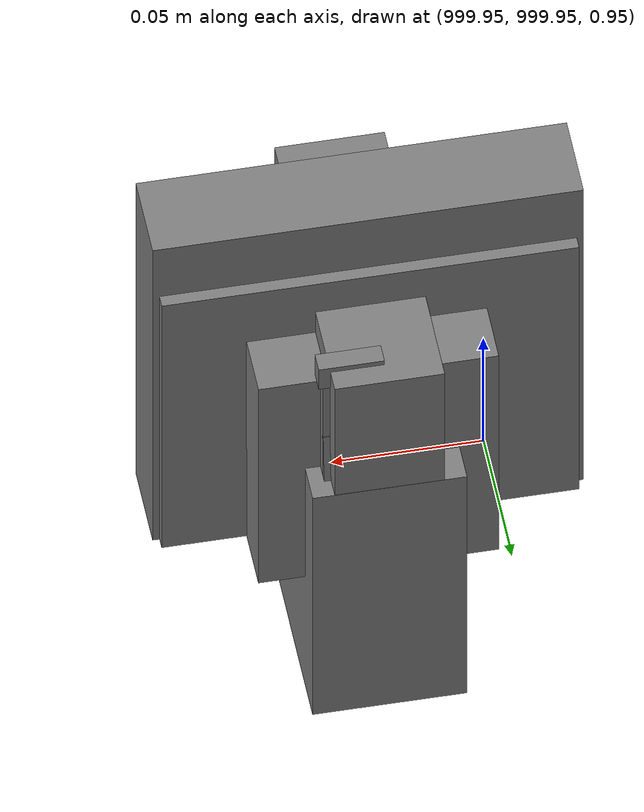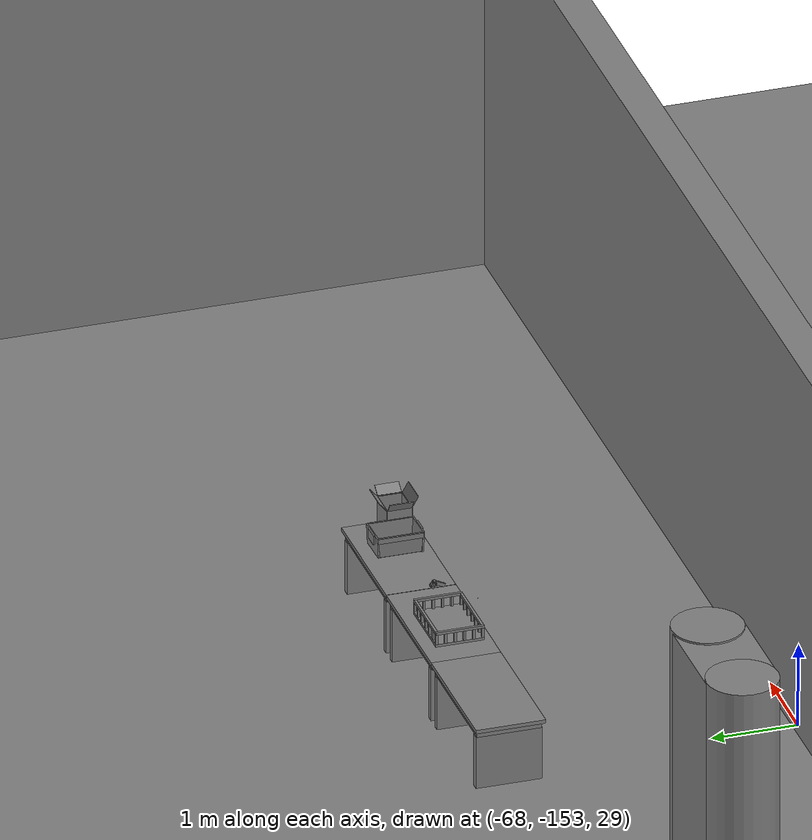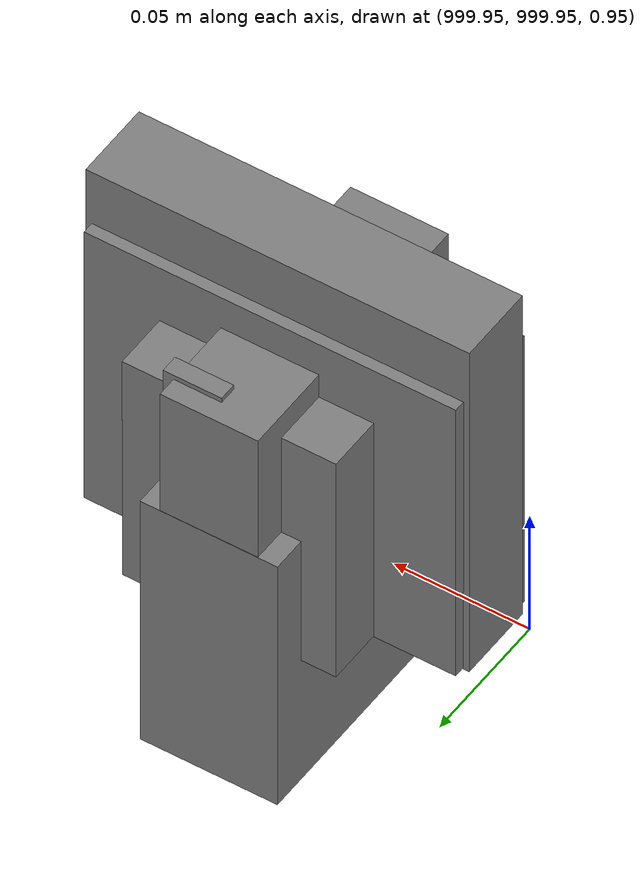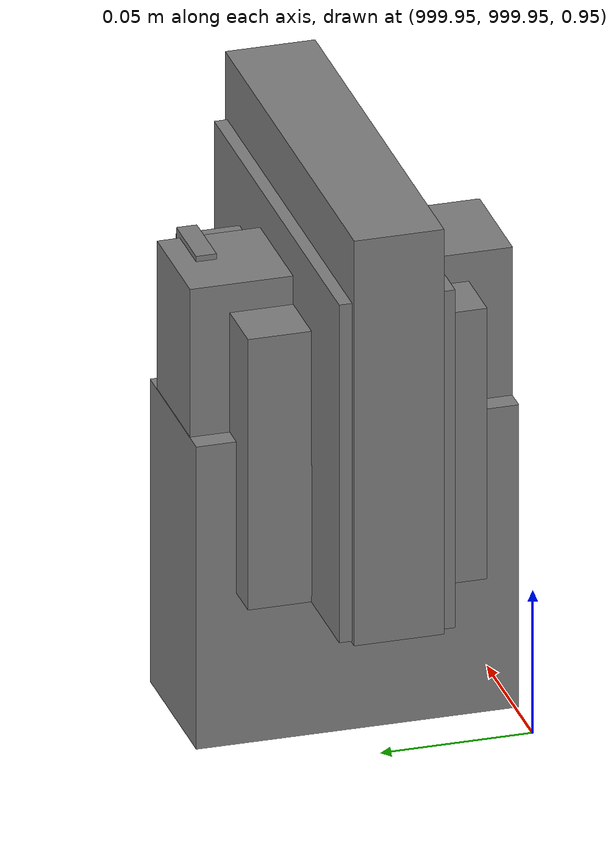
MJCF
<mujoco>
    <option gravity="0.000000000 0.000000000 -9.810000420" timestep="0.0049999999" integrator="implicitfast" density="1.225" viscosity="1.8000001e-05" noslip_iterations="10" iterations="100" sdf_iterations="50">
        <flag multiccd="disable"/>
    </option>
    <size memory="1000M"/>
    <compiler coordinate="local"/>
    <worldbody>
        <light cutoff="30" pos="0 1 1" dir="0 -1 -2"/>
        <light cutoff="30" pos="0 -1 1" dir="0 1 -2"/>
        <body pos="-64.866622925 -149.383972168 30.183746338" euler="89.999984741 89.999946594 0.000000000" name="openloong_gripper_2f85_fix_base_usda_bluebox_01">
            <geom contype="1" conaffinity="1" density="1000" type="box" material="" rgba="0.500000000 0.500000000 0.500000000 1.000000000" solimp="0.899999976 0.949999988 0.001000000" friction="1.000000000 0.005000000 0.000100000" solref="0.020000000 1.000000000" margin="0" condim="3" group="0" pos="0.276580811 0.187225342 0.000068665" quat="0.707106948 0.000077471 0.707106352 0.000077486" size="0.100000001 0.057999998 0.010000000" name="openloong_gripper_2f85_fix_base_usda_geom_66399101_EF0A_4DD5_8E19_3503FA9832CB"/>
            <geom contype="1" conaffinity="1" density="1000" type="box" material="" rgba="0.500000000 0.500000000 0.500000000 1.000000000" solimp="0.899999976 0.949999988 0.001000000" friction="1.000000000 0.005000000 0.000100000" solref="0.020000000 1.000000000" margin="0" condim="3" group="0" pos="0.000000000 0.002883911 0.000000000" quat="0.999999881 0.000000000 0.000000000 0.000000000" size="0.254000008 0.003000000 0.172000006" name="openloong_gripper_2f85_fix_base_usda_geom_52F65653_78C0_4B8E_84D4_691907303F2B"/>
            <geom contype="1" conaffinity="1" density="1000" type="box" material="" rgba="0.500000000 0.500000000 0.500000000 1.000000000" solimp="0.899999976 0.949999988 0.001000000" friction="1.000000000 0.005000000 0.000100000" solref="0.020000000 1.000000000" margin="0" condim="3" group="0" pos="0.000000000 0.124874115 0.173484802" quat="0.999796331 0.020176515 -0.000000015 0.000000030" size="0.259999990 0.119999997 0.007000000" name="openloong_gripper_2f85_fix_base_usda_geom_8B7854D2_5B2D_4B52_B9AB_23C9B89722DC"/>
            <geom contype="1" conaffinity="1" density="1000" type="box" material="" rgba="0.500000000 0.500000000 0.500000000 1.000000000" solimp="0.899999976 0.949999988 0.001000000" friction="1.000000000 0.005000000 0.000100000" solref="0.020000000 1.000000000" margin="0" condim="3" group="0" pos="0.000000000 0.124874115 -0.173469543" quat="0.999796331 -0.020176545 -0.000000015 0.000000000" size="0.259999990 0.119999997 0.007000000" name="openloong_gripper_2f85_fix_base_usda_geom_F986E1E6_D34D_4211_A313_ACBC204E20E7"/>
            <geom contype="1" conaffinity="1" density="1000" type="box" material="" rgba="0.500000000 0.500000000 0.500000000 1.000000000" solimp="0.899999976 0.949999988 0.001000000" friction="1.000000000 0.005000000 0.000100000" solref="0.020000000 1.000000000" margin="0" condim="3" group="0" pos="0.000000000 0.214008331 0.188980103" quat="0.999912977 0.013176724 0.000000015 0.000000000" size="0.259999990 0.029999999 0.012500000" name="openloong_gripper_2f85_fix_base_usda_geom_2540FEED_3CB2_47FF_AF7C_718F307C193D"/>
            <geom contype="1" conaffinity="1" density="1000" type="box" material="" rgba="0.500000000 0.500000000 0.500000000 1.000000000" solimp="0.899999976 0.949999988 0.001000000" friction="1.000000000 0.005000000 0.000100000" solref="0.020000000 1.000000000" margin="0" condim="3" group="0" pos="-0.258361816 0.125289917 0.001876831" quat="0.702796936 -0.020792112 0.710783124 0.020769298" size="0.189999998 0.119999997 0.009000000" name="openloong_gripper_2f85_fix_base_usda_geom_DD7B242B_BD49_4AE5_90A0_0307DD0CDB1C"/>
            <geom contype="1" conaffinity="1" density="1000" type="box" material="" rgba="0.500000000 0.500000000 0.500000000 1.000000000" solimp="0.899999976 0.949999988 0.001000000" friction="1.000000000 0.005000000 0.000100000" solref="0.020000000 1.000000000" margin="0" condim="3" group="0" pos="0.000000000 0.214008331 -0.188980103" quat="0.999912977 -0.013176769 0.000000030 0.000000015" size="0.259999990 0.029999999 0.012500000" name="openloong_gripper_2f85_fix_base_usda_geom_1E42FF4E_4DFD_45D9_83AB_9E13F85F7CA0"/>
            <geom contype="1" conaffinity="1" density="1000" type="box" material="" rgba="0.500000000 0.500000000 0.500000000 1.000000000" solimp="0.899999976 0.949999988 0.001000000" friction="1.000000000 0.005000000 0.000100000" solref="0.020000000 1.000000000" margin="0" condim="3" group="0" pos="-0.276611328 0.187225342 0.000068665" quat="0.707106650 0.000077441 0.707106709 0.000077456" size="0.100000001 0.057999998 0.010000000" name="openloong_gripper_2f85_fix_base_usda_geom_31AAE80A_AB88_48BA_A052_ACD08586703E"/>
            <geom contype="1" conaffinity="1" density="1000" type="box" material="" rgba="0.500000000 0.500000000 0.500000000 1.000000000" solimp="0.899999976 0.949999988 0.001000000" friction="1.000000000 0.005000000 0.000100000" solref="0.020000000 1.000000000" margin="0" condim="3" group="0" pos="0.258331299 0.125289917 0.001876831" quat="0.702851415 0.018856421 0.710823774 -0.019329369" size="0.189999998 0.119999997 0.009000000" name="openloong_gripper_2f85_fix_base_usda_geom_A136A537_9DE9_4610_954A_7BB0D6A4967D"/>
            <freejoint name="openloong_gripper_2f85_fix_base_usda_bluebox_01_joint"/>
            <site size="0.005000000 0.005000000 0.005000000" rgba="0.500000000 0.500000000 0.500000000 1.000000000" pos="0.000000000 0.000000000 0.000000000" quat="0.999961913 0.008726534 0.000000000 0.000000000" group="0" type="sphere" name="openloong_gripper_2f85_fix_base_usda_bluebox_01site"/>
        </body>
        <body pos="-64.496299744 -149.491867065 30.235729218" euler="0.000000000 0.000000000 89.999946594" name="openloong_gripper_2f85_fix_base_usda_cardboardbox_01">
            <geom contype="1" conaffinity="1" density="1000" type="box" material="" rgba="0.500000000 0.500000000 0.500000000 1.000000000" solimp="0.899999976 0.949999988 0.001000000" friction="1.000000000 0.005000000 0.000100000" solref="0.020000000 1.000000000" margin="0" condim="3" group="0" pos="-0.003166199 -0.004086494 0.005052090" quat="1.000000000 0.000000000 0.000000000 0.000000000" size="0.142499998 0.177500010 0.005000000" name="openloong_gripper_2f85_fix_base_usda_geom_D51EF693_9B7F_417B_A44B_08DF8F49B362"/>
            <geom contype="1" conaffinity="1" density="1000" type="box" material="" rgba="0.500000000 0.500000000 0.500000000 1.000000000" solimp="0.899999976 0.949999988 0.001000000" friction="1.000000000 0.005000000 0.000100000" solref="0.020000000 1.000000000" margin="0" condim="3" group="0" pos="-0.003166199 0.170316696 0.150570869" quat="1.000000000 0.000000000 0.000000000 0.000000000" size="0.142499998 0.005000000 0.149999991" name="openloong_gripper_2f85_fix_base_usda_geom_66D76F1D_732E_48C8_A07C_D2CA208463BA"/>
            <geom contype="1" conaffinity="1" density="1000" type="box" material="" rgba="0.500000000 0.500000000 0.500000000 1.000000000" solimp="0.899999976 0.949999988 0.001000000" friction="1.000000000 0.005000000 0.000100000" solref="0.020000000 1.000000000" margin="0" condim="3" group="0" pos="-0.147399902 -0.005307198 0.150570869" quat="1.000000000 0.000000000 0.000000000 0.000000000" size="0.005000000 0.177500010 0.149999991" name="openloong_gripper_2f85_fix_base_usda_geom_70D37644_F72F_4526_A8BA_77942D367F9A"/>
            <geom contype="1" conaffinity="1" density="1000" type="box" material="" rgba="0.500000000 0.500000000 0.500000000 1.000000000" solimp="0.899999976 0.949999988 0.001000000" friction="1.000000000 0.005000000 0.000100000" solref="0.020000000 1.000000000" margin="0" condim="3" group="0" pos="0.140275955 -0.005307198 0.150570869" quat="1.000000000 0.000000000 0.000000000 0.000000000" size="0.005000000 0.177500010 0.149999991" name="openloong_gripper_2f85_fix_base_usda_geom_CFC8CAC7_7C27_448A_A5BE_151216839129"/>
            <geom contype="1" conaffinity="1" density="1000" type="box" material="" rgba="0.500000000 0.500000000 0.500000000 1.000000000" solimp="0.899999976 0.949999988 0.001000000" friction="1.000000000 0.005000000 0.000100000" solref="0.020000000 1.000000000" margin="0" condim="3" group="0" pos="-0.003166199 -0.181550980 0.150570869" quat="1.000000000 0.000000000 0.000000000 0.000000000" size="0.142499998 0.005000000 0.149999991" name="openloong_gripper_2f85_fix_base_usda_geom_C1A702A6_1A9F_4BD3_97E0_D825D855E75E"/>
            <freejoint name="openloong_gripper_2f85_fix_base_usda_cardboardbox_01_joint"/>
            <site size="0.005000000 0.005000000 0.005000000" rgba="0.500000000 0.500000000 0.500000000 1.000000000" pos="0.000000000 0.000000000 0.000000000" quat="0.999961913 0.008726535 0.000000000 0.000000000" group="0" type="sphere" name="openloong_gripper_2f85_fix_base_usda_site_7FB7F5D8_8CC3_4338_80AE_658AACB02568"/>
            <body pos="0.139160156 -0.004048347 0.301930904" euler="-179.999954224 49.383502960 179.999954224" name="openloong_gripper_2f85_fix_base_usda_A1_006">
                <geom contype="1" conaffinity="1" density="1000" type="box" material="" rgba="0.500000000 0.500000000 0.500000000 1.000000000" solimp="0.899999976 0.949999988 0.001000000" friction="1.000000000 0.005000000 0.000100000" solref="0.020000000 1.000000000" margin="0" condim="3" group="0" pos="-0.071587563 0.000009537 0.001745224" quat="0.999999881 0.000000000 0.000000000 0.000000000" size="0.071249999 0.179999992 0.002500000" name="openloong_gripper_2f85_fix_base_usda_geom_37D28496_EB6F_4CAB_8EF1_5D71E89BA1AB"/>
                <joint armature="0" stiffness="0.07" damping="0.0099999998" axis="0.000000 1.000000 0.000000" type="hinge" name="openloong_gripper_2f85_fix_base_usda_A1_006"/>
            </body>
            <body pos="-0.145902634 -0.004086494 0.301938057" euler="-180.000000000 -60.000011444 -180.000000000" name="openloong_gripper_2f85_fix_base_usda_A2_006">
                <geom contype="1" conaffinity="1" density="1000" type="box" material="" rgba="0.500000000 0.500000000 0.500000000 1.000000000" solimp="0.899999976 0.949999988 0.001000000" friction="1.000000000 0.005000000 0.000100000" solref="0.020000000 1.000000000" margin="0" condim="3" group="0" pos="0.071268082 0.000009537 0.002717972" quat="0.000002921 0.000000000 -0.000000030 0.999999881" size="0.071249999 0.179999992 0.002500000" name="openloong_gripper_2f85_fix_base_usda_geom_67DE8164_87E6_4493_BEA4_16358DCA9C88"/>
                <joint armature="0" stiffness="0.07" damping="0.0099999998" axis="0.000000 1.000000 0.000000" type="hinge" name="openloong_gripper_2f85_fix_base_usda_A2_006"/>
            </body>
            <body pos="-0.003385544 0.175991058 0.301930904" euler="-125.858116150 -0.000004561 0.000002331" name="openloong_gripper_2f85_fix_base_usda_B2_006">
                <geom contype="1" conaffinity="1" density="1000" type="box" material="" rgba="0.500000000 0.500000000 0.500000000 1.000000000" solimp="0.899999976 0.949999988 0.001000000" friction="1.000000000 0.005000000 0.000100000" solref="0.020000000 1.000000000" margin="0" condim="3" group="0" pos="0.000009537 -0.070939064 -0.002470016" quat="0.999614120 0.027776197 -0.000000015 0.000000030" size="0.137500003 0.064999998 0.005000000" name="openloong_gripper_2f85_fix_base_usda_geom_4151E7BF_1323_4BE9_9DF2_17246C7A37EB"/>
                <joint armature="0" stiffness="0.07" damping="0.0099999998" axis="1.000000 0.000000 0.000000" type="hinge" name="openloong_gripper_2f85_fix_base_usda_B2_006"/>
            </body>
            <body pos="-0.003385544 -0.184140205 0.301938057" euler="147.805557251 0.000000000 0.000000000" name="openloong_gripper_2f85_fix_base_usda_B1_006">
                <geom contype="1" conaffinity="1" density="1000" type="box" material="" rgba="0.500000000 0.500000000 0.500000000 1.000000000" solimp="0.899999976 0.949999988 0.001000000" friction="1.000000000 0.005000000 0.000100000" solref="0.020000000 1.000000000" margin="0" condim="3" group="0" pos="-0.000028610 0.070202351 -0.002703667" quat="0.999614179 -0.027776167 0.000000000 0.000000000" size="0.137500003 0.064999998 0.005000000" name="openloong_gripper_2f85_fix_base_usda_geom_FAB833ED_F083_409B_A58A_02D4B26F8D21"/>
                <joint armature="0" stiffness="0.07" damping="0.0099999998" axis="1.000000 0.000000 0.000000" type="hinge" name="openloong_gripper_2f85_fix_base_usda_B1_006"/>
            </body>
        </body>
        <body pos="-65.882858276 -149.481979370 30.229999542" euler="-64.487716675 0.000000000 0.000000000" name="openloong_gripper_2f85_fix_base_usda_Barcode">
            <geom contype="1" conaffinity="1" density="1000" type="box" material="" rgba="0.500000000 0.500000000 0.500000000 1.000000000" solimp="0.899999976 0.949999988 0.001000000" friction="1.000000000 0.005000000 0.000100000" solref="0.020000000 1.000000000" margin="0" condim="3" group="0" pos="0.000000000 0.013038635 0.001419067" quat="0.000000000 0.000000000 0.000000000 1.000000119" size="0.034000002 0.010000000 0.017999999" name="openloong_gripper_2f85_fix_base_usda_geom_98E6F406_8E61_4F54_AA96_97BD88772395"/>
            <geom contype="1" conaffinity="1" density="1000" type="box" material="" rgba="0.500000000 0.500000000 0.500000000 1.000000000" solimp="0.899999976 0.949999988 0.001000000" friction="1.000000000 0.005000000 0.000100000" solref="0.020000000 1.000000000" margin="0" condim="3" group="0" pos="0.000000000 -0.035301208 -0.007095337" quat="0.000000000 0.000000000 -0.043619365 0.999048233" size="0.028999999 0.010000000 0.020000000" name="openloong_gripper_2f85_fix_base_usda_geom_44D25298_DDD9_4BA5_89CA_58E580D679A3"/>
            <geom contype="1" conaffinity="1" density="1000" type="box" material="" rgba="0.500000000 0.500000000 0.500000000 1.000000000" solimp="0.899999976 0.949999988 0.001000000" friction="1.000000000 0.005000000 0.000100000" solref="0.020000000 1.000000000" margin="0" condim="3" group="0" pos="0.000000000 -0.043411255 -0.011749268" quat="0.922262907 0.386563420 0.000000000 0.000000000" size="0.026000001 0.010000000 0.020000000" name="openloong_gripper_2f85_fix_base_usda_geom_41AF726B_32F0_4D17_8C84_95C3F6FB89B5"/>
            <geom contype="1" conaffinity="1" density="1000" type="box" material="" rgba="0.500000000 0.500000000 0.500000000 1.000000000" solimp="0.899999976 0.949999988 0.001000000" friction="1.000000000 0.005000000 0.000100000" solref="0.020000000 1.000000000" margin="0" condim="3" group="0" pos="0.000000000 -0.016967773 -0.031860352" quat="0.000000000 0.000000000 0.000000000 1.000000119" size="0.008000000 0.010000000 0.013000000" name="openloong_gripper_2f85_fix_base_usda_geom_FE279B17_500E_42C2_849D_092DA1F950D0"/>
            <geom contype="1" conaffinity="1" density="1000" type="box" material="" rgba="0.500000000 0.500000000 0.500000000 1.000000000" solimp="0.899999976 0.949999988 0.001000000" friction="1.000000000 0.005000000 0.000100000" solref="0.020000000 1.000000000" margin="0" condim="3" group="0" pos="0.000000000 -0.001869202 0.000312805" quat="0.953716993 0.300705761 0.000000000 0.000000000" size="0.032000002 0.010000000 0.018999999" name="openloong_gripper_2f85_fix_base_usda_geom_ABF82433_9FF0_48E7_AE68_46FAACC3E46C"/>
            <geom contype="1" conaffinity="1" density="1000" type="box" material="" rgba="0.500000000 0.500000000 0.500000000 1.000000000" solimp="0.899999976 0.949999988 0.001000000" friction="1.000000000 0.005000000 0.000100000" solref="0.020000000 1.000000000" margin="0" condim="3" group="0" pos="0.000000000 -0.019531250 -0.003173828" quat="0.953716993 0.300705761 0.000000000 0.000000000" size="0.030999999 0.010000000 0.020000000" name="openloong_gripper_2f85_fix_base_usda_geom_CC0C3AFA_9B34_4742_90F1_ED03F96AAB90"/>
            <geom contype="1" conaffinity="1" density="1000" type="box" material="" rgba="0.500000000 0.500000000 0.500000000 1.000000000" solimp="0.899999976 0.949999988 0.001000000" friction="1.000000000 0.005000000 0.000100000" solref="0.020000000 1.000000000" margin="0" condim="3" group="0" pos="0.000000000 -0.035301208 -0.007095337" quat="0.953716993 0.300705761 0.000000000 0.000000000" size="0.028999999 0.010000000 0.020000000" name="openloong_gripper_2f85_fix_base_usda_geom_99A8E978_F8CC_481F_9D52_1DE2F0524F39"/>
            <geom contype="1" conaffinity="1" density="1000" type="box" material="" rgba="0.500000000 0.500000000 0.500000000 1.000000000" solimp="0.899999976 0.949999988 0.001000000" friction="1.000000000 0.005000000 0.000100000" solref="0.020000000 1.000000000" margin="0" condim="3" group="0" pos="0.000000000 -0.042617798 -0.071121216" quat="0.000000000 0.000000000 0.000000000 1.000000119" size="0.013000000 0.021000000 0.059999999" name="openloong_gripper_2f85_fix_base_usda_geom_C3C26346_4863_4198_B6AC_C7EB757F917F"/>
            <freejoint name="openloong_gripper_2f85_fix_base_usda_Barcode_joint"/>
            <site size="0.005000000 0.005000000 0.005000000" rgba="0.500000000 0.500000000 0.500000000 1.000000000" pos="0.000000000 0.000000000 0.000000000" quat="1.000000000 0.000000000 0.000000000 0.000000000" group="0" type="sphere" name="openloong_gripper_2f85_fix_base_usda_Barcode_site"/>
        </body>
        <body pos="-66.745018005 -149.392349243 30.184000015" euler="0.000000000 0.000000000 89.999946594" name="[22330953544025]_Basket_01">
            <geom contype="1" conaffinity="1" density="1000" type="box" material="" rgba="0.500000000 0.500000000 0.500000000 1.000000000" solimp="0.899999976 0.949999988 0.001000000" friction="1.000000000 0.005000000 0.000100000" solref="0.020000000 1.000000000" margin="0" condim="3" group="0" pos="-0.052425385 0.389207840 0.089787483" quat="0.707107008 0.000000000 0.000000000 0.707106411" size="0.014249999 0.014249999 0.059999999" name="[22330953544025]_geom_F49A20CE_512E_41E2_B490_63F83DBDD477"/>
            <geom contype="1" conaffinity="1" density="1000" type="box" material="" rgba="0.500000000 0.500000000 0.500000000 1.000000000" solimp="0.899999976 0.949999988 0.001000000" friction="1.000000000 0.005000000 0.000100000" solref="0.020000000 1.000000000" margin="0" condim="3" group="0" pos="0.264015198 -0.133043289 0.089787483" quat="0.707107008 0.000000000 0.000000000 0.707106411" size="0.014249999 0.014249999 0.059999999" name="[22330953544025]_geom_6942619F_220B_497C_AFC2_FD8F6CCC6B72"/>
            <geom contype="1" conaffinity="1" density="1000" type="box" material="" rgba="0.500000000 0.500000000 0.500000000 1.000000000" solimp="0.899999976 0.949999988 0.001000000" friction="1.000000000 0.005000000 0.000100000" solref="0.020000000 1.000000000" margin="0" condim="3" group="0" pos="-0.264015198 -0.265548706 0.089793205" quat="0.707107008 0.000000000 0.000000000 0.707106411" size="0.014249999 0.014249999 0.059999999" name="[22330953544025]_geom_3B3C15A5_EE64_481C_91E8_3FC777E9F4A9"/>
            <geom contype="1" conaffinity="1" density="1000" type="box" material="" rgba="0.500000000 0.500000000 0.500000000 1.000000000" solimp="0.899999976 0.949999988 0.001000000" friction="1.000000000 0.005000000 0.000100000" solref="0.020000000 1.000000000" margin="0" condim="3" group="0" pos="-0.160263062 -0.389322281 0.089793205" quat="0.707107008 0.000000000 0.000000000 0.707106411" size="0.014249999 0.014249999 0.059999999" name="[22330953544025]_geom_61238BDC_6014_4656_8D92_777DFF26B0D0"/>
            <geom contype="1" conaffinity="1" density="1000" type="box" material="" rgba="0.500000000 0.500000000 0.500000000 1.000000000" solimp="0.899999976 0.949999988 0.001000000" friction="1.000000000 0.005000000 0.000100000" solref="0.020000000 1.000000000" margin="0" condim="3" group="0" pos="0.162265778 -0.389322281 0.089787483" quat="0.707107008 0.000000000 0.000000000 0.707106411" size="0.014249999 0.014249999 0.059999999" name="[22330953544025]_geom_1A54944E_0331_485C_8B72_BB24AF48E551"/>
            <geom contype="1" conaffinity="1" density="1000" type="box" material="" rgba="0.500000000 0.500000000 0.500000000 1.000000000" solimp="0.899999976 0.949999988 0.001000000" friction="1.000000000 0.005000000 0.000100000" solref="0.020000000 1.000000000" margin="0" condim="3" group="0" pos="0.264015198 0.389207840 0.089787483" quat="0.707107008 0.000000000 0.000000000 0.707106411" size="0.014249999 0.014249999 0.059999999" name="[22330953544025]_geom_F1507093_96D5_4795_B356_5253D7EA1937"/>
            <geom contype="1" conaffinity="1" density="1000" type="box" material="" rgba="0.500000000 0.500000000 0.500000000 1.000000000" solimp="0.899999976 0.949999988 0.001000000" friction="1.000000000 0.005000000 0.000100000" solref="0.020000000 1.000000000" margin="0" condim="3" group="0" pos="-0.264015198 -0.133043289 0.089793205" quat="0.707107008 0.000000000 0.000000000 0.707106411" size="0.014249999 0.014249999 0.059999999" name="[22330953544025]_geom_55DD5E03_112C_4438_AF28_036B6859E2D6"/>
            <geom contype="1" conaffinity="1" density="1000" type="box" material="" rgba="0.500000000 0.500000000 0.500000000 1.000000000" solimp="0.899999976 0.949999988 0.001000000" friction="1.000000000 0.005000000 0.000100000" solref="0.020000000 1.000000000" margin="0" condim="3" group="0" pos="-0.264026642 0.269256592 0.089793205" quat="0.707107008 0.000000000 0.000000000 0.707106411" size="0.014249999 0.014249999 0.059999999" name="[22330953544025]_geom_2BDC6D67_9FE5_4D71_A118_C411955A1A5B"/>
            <geom contype="1" conaffinity="1" density="1000" type="box" material="" rgba="0.500000000 0.500000000 0.500000000 1.000000000" solimp="0.899999976 0.949999988 0.001000000" friction="1.000000000 0.005000000 0.000100000" solref="0.020000000 1.000000000" margin="0" condim="3" group="0" pos="0.054462433 0.389207840 0.089787483" quat="0.707107008 0.000000000 0.000000000 0.707106411" size="0.014249999 0.014249999 0.059999999" name="[22330953544025]_geom_3E1A5774_34BA_46CD_BC8C_6F10757FB98D"/>
            <geom contype="1" conaffinity="1" density="1000" type="box" material="" rgba="0.500000000 0.500000000 0.500000000 1.000000000" solimp="0.899999976 0.949999988 0.001000000" friction="1.000000000 0.005000000 0.000100000" solref="0.020000000 1.000000000" margin="0" condim="3" group="0" pos="0.054462433 -0.389322281 0.089787483" quat="0.707107008 0.000000000 0.000000000 0.707106411" size="0.014249999 0.014249999 0.059999999" name="[22330953544025]_geom_B7D54A99_34B8_4E25_957E_9AB02DA3651E"/>
            <geom contype="1" conaffinity="1" density="1000" type="box" material="" rgba="0.500000000 0.500000000 0.500000000 1.000000000" solimp="0.899999976 0.949999988 0.001000000" friction="1.000000000 0.005000000 0.000100000" solref="0.020000000 1.000000000" margin="0" condim="3" group="0" pos="0.264015198 0.269256592 0.089793205" quat="0.707107008 0.000000000 0.000000000 0.707106411" size="0.014249999 0.014249999 0.059999999" name="[22330953544025]_geom_4E223A97_360E_493B_955A_38CEBC286BAB"/>
            <geom contype="1" conaffinity="1" density="1000" type="box" material="" rgba="0.500000000 0.500000000 0.500000000 1.000000000" solimp="0.899999976 0.949999988 0.001000000" friction="1.000000000 0.005000000 0.000100000" solref="0.020000000 1.000000000" margin="0" condim="3" group="0" pos="0.264015198 -0.389322281 0.089787483" quat="0.707107008 0.000000000 0.000000000 0.707106411" size="0.014249999 0.014249999 0.059999999" name="[22330953544025]_geom_A2E61DDE_9454_48A2_B534_9C2FDF87296C"/>
            <geom contype="1" conaffinity="1" density="1000" type="box" material="" rgba="0.500000000 0.500000000 0.500000000 1.000000000" solimp="0.899999976 0.949999988 0.001000000" friction="1.000000000 0.005000000 0.000100000" solref="0.020000000 1.000000000" margin="0" condim="3" group="0" pos="0.000000000 0.000000000 0.015998840" quat="0.707107008 0.000000000 0.000000000 0.707106411" size="0.403499991 0.279000014 0.015750000" name="[22330953544025]_geom_2E3D87BA_368B_4E41_9CF5_7BCB019DB1E4"/>
            <geom contype="1" conaffinity="1" density="1000" type="box" material="" rgba="0.500000000 0.500000000 0.500000000 1.000000000" solimp="0.899999976 0.949999988 0.001000000" friction="1.000000000 0.005000000 0.000100000" solref="0.020000000 1.000000000" margin="0" condim="3" group="0" pos="0.000000000 -0.389476776 0.163619041" quat="0.707107008 0.000000000 0.000000000 0.707106411" size="0.015000000 0.277500004 0.015750000" name="[22330953544025]_geom_ABFCC25F_DEC6_4EBB_B726_2A8E47E8AFED"/>
            <geom contype="1" conaffinity="1" density="1000" type="box" material="" rgba="0.500000000 0.500000000 0.500000000 1.000000000" solimp="0.899999976 0.949999988 0.001000000" friction="1.000000000 0.005000000 0.000100000" solref="0.020000000 1.000000000" margin="0" condim="3" group="0" pos="0.162265778 0.389207840 0.089787483" quat="0.707107008 0.000000000 0.000000000 0.707106411" size="0.014249999 0.014249999 0.059999999" name="[22330953544025]_geom_C4FFAF43_D9C2_42D9_9B53_04B5E6B4C85E"/>
            <geom contype="1" conaffinity="1" density="1000" type="box" material="" rgba="0.500000000 0.500000000 0.500000000 1.000000000" solimp="0.899999976 0.949999988 0.001000000" friction="1.000000000 0.005000000 0.000100000" solref="0.020000000 1.000000000" margin="0" condim="3" group="0" pos="0.000000000 0.389471054 0.163619041" quat="0.707107008 0.000000000 0.000000000 0.707106411" size="0.015000000 0.277500004 0.015750000" name="[22330953544025]_geom_A32C52B0_35B3_4431_A2C2_F7F34DE95FA3"/>
            <geom contype="1" conaffinity="1" density="1000" type="box" material="" rgba="0.500000000 0.500000000 0.500000000 1.000000000" solimp="0.899999976 0.949999988 0.001000000" friction="1.000000000 0.005000000 0.000100000" solref="0.020000000 1.000000000" margin="0" condim="3" group="0" pos="-0.263511658 0.000000000 0.163619041" quat="0.707107008 0.000000000 0.000000000 0.707106411" size="0.403499991 0.015000000 0.015750000" name="[22330953544025]_geom_D869B91B_743E_43D2_A55E_FD72B23F5E56"/>
            <geom contype="1" conaffinity="1" density="1000" type="box" material="" rgba="0.500000000 0.500000000 0.500000000 1.000000000" solimp="0.899999976 0.949999988 0.001000000" friction="1.000000000 0.005000000 0.000100000" solref="0.020000000 1.000000000" margin="0" condim="3" group="0" pos="-0.264015198 0.141334534 0.089793205" quat="0.707107008 0.000000000 0.000000000 0.707106411" size="0.014249999 0.014249999 0.059999999" name="[22330953544025]_geom_71C9DBEA_3AFE_40CD_B4D3_28F1F2FED0B4"/>
            <geom contype="1" conaffinity="1" density="1000" type="box" material="" rgba="0.500000000 0.500000000 0.500000000 1.000000000" solimp="0.899999976 0.949999988 0.001000000" friction="1.000000000 0.005000000 0.000100000" solref="0.020000000 1.000000000" margin="0" condim="3" group="0" pos="0.264015198 -0.265548706 0.089787483" quat="0.707107008 0.000000000 0.000000000 0.707106411" size="0.014249999 0.014249999 0.059999999" name="[22330953544025]_geom_A5E87F14_2E1A_4A38_96EE_7B502C8F9F91"/>
            <geom contype="1" conaffinity="1" density="1000" type="box" material="" rgba="0.500000000 0.500000000 0.500000000 1.000000000" solimp="0.899999976 0.949999988 0.001000000" friction="1.000000000 0.005000000 0.000100000" solref="0.020000000 1.000000000" margin="0" condim="3" group="0" pos="-0.160263062 0.389207840 0.089787483" quat="0.707107008 0.000000000 0.000000000 0.707106411" size="0.014249999 0.014249999 0.059999999" name="[22330953544025]_geom_5810E68F_8E51_43AF_9A01_11320E284FEB"/>
            <geom contype="1" conaffinity="1" density="1000" type="box" material="" rgba="0.500000000 0.500000000 0.500000000 1.000000000" solimp="0.899999976 0.949999988 0.001000000" friction="1.000000000 0.005000000 0.000100000" solref="0.020000000 1.000000000" margin="0" condim="3" group="0" pos="-0.052425385 -0.389322281 0.089787483" quat="0.707107008 0.000000000 0.000000000 0.707106411" size="0.014249999 0.014249999 0.059999999" name="[22330953544025]_geom_70108C91_9EC5_4009_BE92_54750550DB74"/>
            <geom contype="1" conaffinity="1" density="1000" type="box" material="" rgba="0.500000000 0.500000000 0.500000000 1.000000000" solimp="0.899999976 0.949999988 0.001000000" friction="1.000000000 0.005000000 0.000100000" solref="0.020000000 1.000000000" margin="0" condim="3" group="0" pos="-0.264026642 -0.389322281 0.089793205" quat="0.707107008 0.000000000 0.000000000 0.707106411" size="0.014249999 0.014249999 0.059999999" name="[22330953544025]_geom_4ACD75B0_FF70_4E65_A2B3_80DBEBB79C4C"/>
            <geom contype="1" conaffinity="1" density="1000" type="box" material="" rgba="0.500000000 0.500000000 0.500000000 1.000000000" solimp="0.899999976 0.949999988 0.001000000" friction="1.000000000 0.005000000 0.000100000" solref="0.020000000 1.000000000" margin="0" condim="3" group="0" pos="0.264015198 0.141334534 0.089787483" quat="0.707107008 0.000000000 0.000000000 0.707106411" size="0.014249999 0.014249999 0.059999999" name="[22330953544025]_geom_FEFD9D18_8021_44F0_89C7_0195AFA0EE59"/>
            <geom contype="1" conaffinity="1" density="1000" type="box" material="" rgba="0.500000000 0.500000000 0.500000000 1.000000000" solimp="0.899999976 0.949999988 0.001000000" friction="1.000000000 0.005000000 0.000100000" solref="0.020000000 1.000000000" margin="0" condim="3" group="0" pos="-0.264015198 0.389207840 0.089793205" quat="0.707107008 0.000000000 0.000000000 0.707106411" size="0.014249999 0.014249999 0.059999999" name="[22330953544025]_geom_FC994375_4031_4D3E_90C2_6DAA4DD10D00"/>
            <geom contype="1" conaffinity="1" density="1000" type="box" material="" rgba="0.500000000 0.500000000 0.500000000 1.000000000" solimp="0.899999976 0.949999988 0.001000000" friction="1.000000000 0.005000000 0.000100000" solref="0.020000000 1.000000000" margin="0" condim="3" group="0" pos="0.264015198 0.004480362 0.089787483" quat="0.707107008 0.000000000 0.000000000 0.707106411" size="0.014249999 0.014249999 0.059999999" name="[22330953544025]_geom_000E105D_55B1_4BAA_B035_F23C1BE4BBA5"/>
            <geom contype="1" conaffinity="1" density="1000" type="box" material="" rgba="0.500000000 0.500000000 0.500000000 1.000000000" solimp="0.899999976 0.949999988 0.001000000" friction="1.000000000 0.005000000 0.000100000" solref="0.020000000 1.000000000" margin="0" condim="3" group="0" pos="0.263694763 -0.000011444 0.163619041" quat="0.707107008 0.000000000 0.000000000 0.707106411" size="0.403499991 0.015000000 0.015750000" name="[22330953544025]_geom_4C1F049B_95AC_4AC2_91C5_79DA03B2DFD2"/>
            <geom contype="1" conaffinity="1" density="1000" type="box" material="" rgba="0.500000000 0.500000000 0.500000000 1.000000000" solimp="0.899999976 0.949999988 0.001000000" friction="1.000000000 0.005000000 0.000100000" solref="0.020000000 1.000000000" margin="0" condim="3" group="0" pos="-0.264015198 0.004480362 0.089793205" quat="0.707107008 0.000000000 0.000000000 0.707106411" size="0.014249999 0.014249999 0.059999999" name="[22330953544025]_geom_8E82AC94_D801_41EE_A908_C8F8911810FF"/>
            <freejoint name="[22330953544025]_joint_47AFD22C_518E_4CBC_80E4_2DFB74A6DE3C"/>
        </body>
        <body pos="0.000000000 0.000000000 0.000000000" euler="0.000000000 0.000000000 0.000000000" name="Static Objects_Static Objects">
            <geom contype="1" conaffinity="1" density="1000" type="box" material="" rgba="0.500000000 0.500000000 0.500000000 1.000000000" solimp="0.899999976 0.949999988 0.001000000" friction="1.000000000 0.005000000 0.000100000" solref="0.020000000 1.000000000" margin="0" condim="3" group="0" pos="-67.544113159 -149.365814209 29.727830887" quat="0.500000417 0.499999970 0.499999553 0.499999970" size="0.381000012 0.319999993 0.041000001" name="Static Objects_geom_15B944D3_9827_43E7_84D7_F4834347C5DD"/>
            <geom contype="1" conaffinity="1" density="1000" type="box" material="" rgba="0.500000000 0.500000000 0.500000000 1.000000000" solimp="0.899999976 0.949999988 0.001000000" friction="1.000000000 0.005000000 0.000100000" solref="0.020000000 1.000000000" margin="0" condim="3" group="0" pos="-68.239501953 -149.365814209 30.086868286" quat="0.500000417 0.499999970 0.499999553 0.499999970" size="0.370999992 0.039500002 0.745000005" name="Static Objects_geom_C9ABF737_9967_485B_AABA_B2F9A3EA7F11"/>
            <geom contype="1" conaffinity="1" density="1000" type="box" material="" rgba="0.500000000 0.500000000 0.500000000 1.000000000" solimp="0.899999976 0.949999988 0.001000000" friction="1.000000000 0.005000000 0.000100000" solref="0.020000000 1.000000000" margin="0" condim="3" group="0" pos="-68.239501953 -149.365814209 30.147235870" quat="0.500000417 0.499999970 0.499999553 0.499999970" size="0.400000006 0.022000000 0.800000012" name="Static Objects_geom_6F2E8309_AC05_4BDF_BAB3_65D1217F117E"/>
            <geom contype="1" conaffinity="1" density="1000" type="box" material="" rgba="0.500000000 0.500000000 0.500000000 1.000000000" solimp="0.899999976 0.949999988 0.001000000" friction="1.000000000 0.005000000 0.000100000" solref="0.020000000 1.000000000" margin="0" condim="3" group="0" pos="-68.934890747 -149.365814209 29.727830887" quat="0.500000417 0.499999970 0.499999553 0.499999970" size="0.381000012 0.319999993 0.041000001" name="Static Objects_geom_046507D9_B1D9_42A2_BD69_EA49237D2A07"/>
            <geom contype="1" conaffinity="1" density="1000" type="box" material="" rgba="0.500000000 0.500000000 0.500000000 1.000000000" solimp="0.899999976 0.949999988 0.001000000" friction="1.000000000 0.005000000 0.000100000" solref="0.020000000 1.000000000" margin="0" condim="3" group="0" pos="-68.239501953 -149.365814209 29.561563492" quat="0.500000417 0.499999970 0.499999553 0.499999970" size="0.020000000 0.022000000 0.660000026" name="Static Objects_geom_3CB4A63A_B223_458E_BC76_5CDC9217E288"/>
            <geom contype="1" conaffinity="1" density="1000" type="box" material="" rgba="0.500000000 0.500000000 0.500000000 1.000000000" solimp="0.899999976 0.949999988 0.001000000" friction="1.000000000 0.005000000 0.000100000" solref="0.020000000 1.000000000" margin="0" condim="3" group="0" pos="-65.945671082 -149.365814209 29.727830887" quat="0.500000417 0.499999970 0.499999553 0.499999970" size="0.381000012 0.319999993 0.041000001" name="Static Objects_geom_5AF6A543_2676_4A26_9349_0300612FB21D"/>
            <geom contype="1" conaffinity="1" density="1000" type="box" material="" rgba="0.500000000 0.500000000 0.500000000 1.000000000" solimp="0.899999976 0.949999988 0.001000000" friction="1.000000000 0.005000000 0.000100000" solref="0.020000000 1.000000000" margin="0" condim="3" group="0" pos="-66.641059875 -149.365814209 30.086868286" quat="0.500000417 0.499999970 0.499999553 0.499999970" size="0.370999992 0.039500002 0.745000005" name="Static Objects_geom_2FE660C9_200E_4915_BAB0_FECE2E5D6128"/>
            <geom contype="1" conaffinity="1" density="1000" type="box" material="" rgba="0.500000000 0.500000000 0.500000000 1.000000000" solimp="0.899999976 0.949999988 0.001000000" friction="1.000000000 0.005000000 0.000100000" solref="0.020000000 1.000000000" margin="0" condim="3" group="0" pos="-66.641059875 -149.365814209 30.147235870" quat="0.500000417 0.499999970 0.499999553 0.499999970" size="0.400000006 0.022000000 0.800000012" name="Static Objects_geom_FABFEB09_C77E_44CD_BB4C_FB3549ADFAD9"/>
            <geom contype="1" conaffinity="1" density="1000" type="box" material="" rgba="0.500000000 0.500000000 0.500000000 1.000000000" solimp="0.899999976 0.949999988 0.001000000" friction="1.000000000 0.005000000 0.000100000" solref="0.020000000 1.000000000" margin="0" condim="3" group="0" pos="-67.336448669 -149.365814209 29.727830887" quat="0.500000417 0.499999970 0.499999553 0.499999970" size="0.381000012 0.319999993 0.041000001" name="Static Objects_geom_BB889015_EA87_40A8_8999_C3A0E77183C2"/>
            <geom contype="1" conaffinity="1" density="1000" type="box" material="" rgba="0.500000000 0.500000000 0.500000000 1.000000000" solimp="0.899999976 0.949999988 0.001000000" friction="1.000000000 0.005000000 0.000100000" solref="0.020000000 1.000000000" margin="0" condim="3" group="0" pos="-66.641059875 -149.365814209 29.561563492" quat="0.500000417 0.499999970 0.499999553 0.499999970" size="0.020000000 0.022000000 0.660000026" name="Static Objects_geom_24CF7B87_2EE7_4092_ACB6_3B51200DB1F5"/>
            <geom contype="1" conaffinity="1" density="1000" type="box" material="" rgba="0.500000000 0.500000000 0.500000000 1.000000000" solimp="0.899999976 0.949999988 0.001000000" friction="1.000000000 0.005000000 0.000100000" solref="0.020000000 1.000000000" margin="0" condim="3" group="0" pos="-64.338577271 -149.365814209 29.727830887" quat="0.500000417 0.499999970 0.499999553 0.499999970" size="0.381000012 0.319999993 0.041000001" name="Static Objects_geom_9E4B2AE7_CC1E_4963_A884_A2606A093F7B"/>
            <geom contype="1" conaffinity="1" density="1000" type="box" material="" rgba="0.500000000 0.500000000 0.500000000 1.000000000" solimp="0.899999976 0.949999988 0.001000000" friction="1.000000000 0.005000000 0.000100000" solref="0.020000000 1.000000000" margin="0" condim="3" group="0" pos="-65.033966064 -149.365814209 30.086868286" quat="0.500000417 0.499999970 0.499999553 0.499999970" size="0.370999992 0.039500002 0.745000005" name="Static Objects_geom_0636CA83_B6DF_45B3_8ABD_BA9636C5EAC3"/>
            <geom contype="1" conaffinity="1" density="1000" type="box" material="" rgba="0.500000000 0.500000000 0.500000000 1.000000000" solimp="0.899999976 0.949999988 0.001000000" friction="1.000000000 0.005000000 0.000100000" solref="0.020000000 1.000000000" margin="0" condim="3" group="0" pos="-65.033966064 -149.365814209 30.147235870" quat="0.500000417 0.499999970 0.499999553 0.499999970" size="0.400000006 0.022000000 0.800000012" name="Static Objects_geom_8713F650_D98B_4A3D_AE4F_D011D4BF30F4"/>
            <geom contype="1" conaffinity="1" density="1000" type="box" material="" rgba="0.500000000 0.500000000 0.500000000 1.000000000" solimp="0.899999976 0.949999988 0.001000000" friction="1.000000000 0.005000000 0.000100000" solref="0.020000000 1.000000000" margin="0" condim="3" group="0" pos="-65.729354858 -149.365814209 29.727830887" quat="0.500000417 0.499999970 0.499999553 0.499999970" size="0.381000012 0.319999993 0.041000001" name="Static Objects_geom_F7BF0503_7856_43F4_9FA8_D2C03FFD7105"/>
            <geom contype="1" conaffinity="1" density="1000" type="box" material="" rgba="0.500000000 0.500000000 0.500000000 1.000000000" solimp="0.899999976 0.949999988 0.001000000" friction="1.000000000 0.005000000 0.000100000" solref="0.020000000 1.000000000" margin="0" condim="3" group="0" pos="-65.033966064 -149.365814209 29.561563492" quat="0.500000417 0.499999970 0.499999553 0.499999970" size="0.020000000 0.022000000 0.660000026" name="Static Objects_geom_022658E2_8F40_4460_BC27_BC0E79F739AF"/>
            <geom contype="1" conaffinity="1" density="1000" type="box" material="" rgba="0.500000000 0.500000000 0.500000000 1.000000000" solimp="0.899999976 0.949999988 0.001000000" friction="1.000000000 0.005000000 0.000100000" solref="0.020000000 1.000000000" margin="0" condim="3" group="0" pos="-61.754566193 -137.853729248 33.906845093" quat="0.707107067 0.000000000 0.000000000 0.707106471" size="0.759999990 0.759999990 4.500000000" name="Static Objects_geom_A50B822A_2A7A_4087_99EA_B251C6FF6EBB"/>
            <geom contype="1" conaffinity="1" density="1000" type="box" material="" rgba="0.500000000 0.500000000 0.500000000 1.000000000" solimp="0.899999976 0.949999988 0.001000000" friction="1.000000000 0.005000000 0.000100000" solref="0.020000000 1.000000000" margin="0" condim="3" group="0" pos="-57.511135101 -144.927108765 31.707921982" quat="1.000000000 0.000000000 0.000000000 0.000000000" size="0.200000003 8.000000000 2.299999952" name="Static Objects_geom_21633350_722D_475E_B763_F4BA03CEE6DE"/>
            <geom contype="1" conaffinity="1" density="1000" type="box" material="" rgba="0.500000000 0.500000000 0.500000000 1.000000000" solimp="0.899999976 0.949999988 0.001000000" friction="1.000000000 0.005000000 0.000100000" solref="0.020000000 1.000000000" margin="0" condim="3" group="0" pos="-80.517646790 -157.574050903 31.688196182" quat="0.707107067 0.000000000 0.000000000 0.707106471" size="0.600000024 0.600000024 2.299999952" name="Static Objects_geom_7BFCBB53_BCE1_4209_8794_E447DA0F482B"/>
            <geom contype="1" conaffinity="1" density="1000" type="box" material="" rgba="0.500000000 0.500000000 0.500000000 1.000000000" solimp="0.899999976 0.949999988 0.001000000" friction="1.000000000 0.005000000 0.000100000" solref="0.020000000 1.000000000" margin="0" condim="3" group="0" pos="-80.711044312 -147.414932251 31.666158676" quat="1.000000000 0.000000000 0.000000000 0.000000000" size="0.200000003 10.000000000 2.299999952" name="Static Objects_geom_1C68BDA0_42F0_4764_82E0_FF0F2AF7F895"/>
            <geom contype="1" conaffinity="1" density="1000" type="box" material="" rgba="0.500000000 0.500000000 0.500000000 1.000000000" solimp="0.899999976 0.949999988 0.001000000" friction="1.000000000 0.005000000 0.000100000" solref="0.020000000 1.000000000" margin="0" condim="3" group="0" pos="-57.687217712 -137.434692383 31.688196182" quat="0.707107067 0.000000000 0.000000000 0.707106471" size="0.600000024 0.600000024 2.299999952" name="Static Objects_geom_7193717F_E826_4FAD_8AF6_E4B4F78302C1"/>
            <geom contype="1" conaffinity="1" density="1000" type="box" material="" rgba="0.500000000 0.500000000 0.500000000 1.000000000" solimp="0.899999976 0.949999988 0.001000000" friction="1.000000000 0.005000000 0.000100000" solref="0.020000000 1.000000000" margin="0" condim="3" group="0" pos="-69.537033081 -140.263229370 31.714921951" quat="0.707107067 0.000000000 0.000000000 0.707106471" size="0.759999990 4.500000000 2.299999952" name="Static Objects_geom_239CF26B_80F3_4B53_BC7B_F8F5C46AFFAF"/>
            <geom contype="1" conaffinity="1" density="1000" type="box" material="" rgba="0.500000000 0.500000000 0.500000000 1.000000000" solimp="0.899999976 0.949999988 0.001000000" friction="1.000000000 0.005000000 0.000100000" solref="0.020000000 1.000000000" margin="0" condim="3" group="0" pos="-80.073638916 -137.853713989 33.906845093" quat="0.707107067 0.000000000 0.000000000 0.707106471" size="0.759999990 0.759999990 4.500000000" name="Static Objects_geom_EC11D232_64A6_4A47_B572_E06D856C3E3F"/>
            <geom contype="1" conaffinity="1" density="1000" type="box" material="" rgba="0.500000000 0.500000000 0.500000000 1.000000000" solimp="0.899999976 0.949999988 0.001000000" friction="1.000000000 0.005000000 0.000100000" solref="0.020000000 1.000000000" margin="0" condim="3" group="0" pos="-73.406707764 -155.734664917 31.707921982" quat="1.000000000 0.000000000 0.000000000 0.000000000" size="0.200000003 3.000000000 2.299999952" name="Static Objects_geom_677DC534_3F18_494E_9A97_A8F487580815"/>
            <geom contype="1" conaffinity="1" density="1000" type="box" material="" rgba="0.500000000 0.500000000 0.500000000 1.000000000" solimp="0.899999976 0.949999988 0.001000000" friction="1.000000000 0.005000000 0.000100000" solref="0.020000000 1.000000000" margin="0" condim="3" group="0" pos="-68.497543335 -137.448257446 31.707921982" quat="0.707107067 0.000000000 0.000000000 0.707106471" size="0.200000003 14.000000000 2.299999952" name="Static Objects_geom_50613DAF_4001_4811_9123_3FB93D916048"/>
            <geom contype="1" conaffinity="1" density="1000" type="cylinder" material="" rgba="0.500000000 0.500000000 0.500000000 1.000000000" solimp="0.899999976 0.949999988 0.001000000" friction="1.000000000 0.005000000 0.000100000" solref="0.020000000 1.000000000" margin="0" condim="3" group="0" pos="-68.868522644 -142.134506226 31.711090088" quat="0.707107067 0.000000000 0.000000000 0.707106471" size="0.509999990 2.299999952 1.000000000" name="Static Objects_geom_BB4B95A8_12A2_4239_B1F6_65CA92C4C8E5"/>
            <geom contype="1" conaffinity="1" density="1000" type="plane" material="" rgba="0.500000000 0.500000000 0.500000000 1.000000000" solimp="0.899999976 0.949999988 0.001000000" friction="1.000000000 0.005000000 0.000100000" solref="0.020000000 1.000000000" margin="0" condim="3" group="0" pos="-72.873703003 -147.131927490 29.409669876" quat="1.000000000 0.000000000 0.000000000 0.000000000" size="18.000000000 14.000000000 1.000000000" name="Static Objects_geom_B920E680_CD2B_4C0B_930E_98EDD30BFE21"/>
            <geom contype="1" conaffinity="1" density="1000" type="box" material="" rgba="0.500000000 0.500000000 0.500000000 1.000000000" solimp="0.899999976 0.949999988 0.001000000" friction="1.000000000 0.005000000 0.000100000" solref="0.020000000 1.000000000" margin="0" condim="3" group="0" pos="-79.943580627 -157.782272339 31.707921982" quat="0.707107067 0.000000000 0.000000000 0.707106471" size="0.200000003 7.000000000 2.299999952" name="Static Objects_geom_B24CEED6_8B3D_4E17_BC02_17DBA3281696"/>
            <geom contype="1" conaffinity="1" density="1000" type="box" material="" rgba="0.500000000 0.500000000 0.500000000 1.000000000" solimp="0.899999976 0.949999988 0.001000000" friction="1.000000000 0.005000000 0.000100000" solref="0.020000000 1.000000000" margin="0" condim="3" group="0" pos="-65.421028137 -152.903442383 31.707921982" quat="0.707107067 0.000000000 0.000000000 0.707106471" size="0.200000003 7.800000191 2.299999952" name="Static Objects_geom_1846598E_1FC0_4352_8A2B_B9BBD3670444"/>
            <geom contype="1" conaffinity="1" density="1000" type="box" material="" rgba="0.500000000 0.500000000 0.500000000 1.000000000" solimp="0.899999976 0.949999988 0.001000000" friction="1.000000000 0.005000000 0.000100000" solref="0.020000000 1.000000000" margin="0" condim="3" group="0" pos="-74.776908875 -149.964416504 31.688196182" quat="1.000000000 0.000000000 0.000000000 0.000000000" size="0.600000024 0.409999996 2.299999952" name="Static Objects_geom_465EB26A_A2B6_4859_A1A8_C5035418A85D"/>
            <geom contype="1" conaffinity="1" density="1000" type="cylinder" material="" rgba="0.500000000 0.500000000 0.500000000 1.000000000" solimp="0.899999976 0.949999988 0.001000000" friction="1.000000000 0.005000000 0.000100000" solref="0.020000000 1.000000000" margin="0" condim="3" group="0" pos="-60.161884308 -142.134506226 31.711090088" quat="0.707107067 0.000000000 0.000000000 0.707106471" size="0.509999990 2.299999952 1.000000000" name="Static Objects_geom_6AA6E12D_A5C4_42C8_A3E6_C0469794DCF4"/>
            <geom contype="1" conaffinity="1" density="1000" type="cylinder" material="" rgba="0.500000000 0.500000000 0.500000000 1.000000000" solimp="0.899999976 0.949999988 0.001000000" friction="1.000000000 0.005000000 0.000100000" solref="0.020000000 1.000000000" margin="0" condim="3" group="0" pos="-75.382453918 -149.963455200 31.711090088" quat="0.707107067 0.000000000 0.000000000 0.707106471" size="0.409999996 2.299999952 1.000000000" name="Static Objects_geom_EF0F053E_C193_4E3E_9B8B_F801A2311170"/>
            <geom contype="1" conaffinity="1" density="1000" type="cylinder" material="" rgba="0.500000000 0.500000000 0.500000000 1.000000000" solimp="0.899999976 0.949999988 0.001000000" friction="1.000000000 0.005000000 0.000100000" solref="0.020000000 1.000000000" margin="0" condim="3" group="0" pos="-74.154960632 -149.963455200 31.711090088" quat="0.707107067 0.000000000 0.000000000 0.707106471" size="0.409999996 2.299999952 1.000000000" name="Static Objects_geom_E72F8C29_FEBA_4894_8E3E_E74026199A87"/>
            <geom contype="1" conaffinity="1" density="1000" type="cylinder" material="" rgba="0.500000000 0.500000000 0.500000000 1.000000000" solimp="0.899999976 0.949999988 0.001000000" friction="1.000000000 0.005000000 0.000100000" solref="0.020000000 1.000000000" margin="0" condim="3" group="0" pos="-77.566612244 -142.134506226 31.711090088" quat="0.707107067 0.000000000 0.000000000 0.707106471" size="0.509999990 2.299999952 1.000000000" name="Static Objects_geom_F0466A37_7932_48B1_BD3B_FFEF9F7B72C9"/>
        </body>
        <body pos="-66.306831360 -149.464523315 31.165622711" euler="-25.328420639 70.121109009 -23.416925430" mocap="true" name="spotlight6_SpotLight"/>
        <body pos="1000.000000000 1000.000000000 1.000000000" euler="0.000000000 0.000000000 180.000000000" name="openloong_gripper_2f85_fix_base_usda_wifi_box">
            <geom contype="1" conaffinity="1" density="1000" type="box" material="" rgba="0.500000000 0.500000000 0.500000000 1.000000000" solimp="0.899999976 0.949999988 0.001000000" friction="1.000000000 0.005000000 0.000100000" solref="0.020000000 1.000000000" margin="0" condim="3" group="0" pos="0.000000000 0.000000000 0.058978677" quat="0.000000000 0.000000047 0.000000000 1.000000000" size="0.068499997 0.018999999 0.059000000" name="openloong_gripper_2f85_fix_base_usda_geom_5A6C8C33_92E0_4CA7_A08E_18DF723D3295"/>
            <freejoint name="openloong_gripper_2f85_fix_base_usda_wifi_box_joint"/>
            <site size="0.005000000 0.005000000 0.005000000" rgba="0.500000000 0.500000000 0.500000000 1.000000000" pos="0.000000000 0.000000000 0.000000000" quat="0.999961913 0.008726500 0.000000000 0.000000000" group="0" type="sphere" name="openloong_gripper_2f85_fix_base_usda_wifi_boxsite"/>
        </body>
        <body pos="1000.000000000 1000.000000000 1.000000000" euler="0.000000000 0.000000000 180.000000000" name="openloong_gripper_2f85_fix_base_usda_cpu_fan">
            <geom contype="1" conaffinity="1" density="1000" type="box" material="" rgba="0.500000000 0.500000000 0.500000000 1.000000000" solimp="0.899999976 0.949999988 0.001000000" friction="1.000000000 0.005000000 0.000100000" solref="0.020000000 1.000000000" margin="0" condim="3" group="0" pos="0.000000000 0.000000000 0.070034981" quat="0.000000000 0.000000000 0.000000000 1.000000000" size="0.070700005 0.014699999 0.070700005" name="openloong_gripper_2f85_fix_base_usda_geom_96C969F9_689A_4295_8D18_239BC54B9325"/>
            <freejoint name="openloong_gripper_2f85_fix_base_usda_cpu_fan_joint"/>
            <site size="0.005000000 0.005000000 0.005000000" rgba="0.500000000 0.500000000 0.500000000 1.000000000" pos="0.000000000 0.000000000 0.000000000" quat="0.999961913 0.008726535 0.000000000 0.000000000" group="0" type="sphere" name="openloong_gripper_2f85_fix_base_usda_cpu_fancsite"/>
        </body>
        <body pos="-65.981285095 -148.879455566 31.171249390" euler="-111.645004272 42.006282806 -10.140127182" mocap="true" name="spotlight3_SpotLight"/>
        <body pos="1000.000000000 1000.000000000 1.000000000" euler="0.000000000 0.000000000 180.000000000" name="openloong_gripper_2f85_fix_base_usda_battery_01">
            <geom contype="1" conaffinity="1" density="1000" type="box" material="" rgba="0.500000000 0.500000000 0.500000000 1.000000000" solimp="0.899999976 0.949999988 0.001000000" friction="1.000000000 0.005000000 0.000100000" solref="0.020000000 1.000000000" margin="0" condim="3" group="0" pos="-0.011123657 -0.041940309 0.101691343" quat="1.000000000 0.000000000 0.000000000 0.000000000" size="0.010800000 0.003375000 0.004725000" name="openloong_gripper_2f85_fix_base_usda_geom_140BB47E_2B04_4B2C_A9D2_74E86DEFD965"/>
            <geom contype="1" conaffinity="1" density="1000" type="box" material="" rgba="0.500000000 0.500000000 0.500000000 1.000000000" solimp="0.899999976 0.949999988 0.001000000" friction="1.000000000 0.005000000 0.000100000" solref="0.020000000 1.000000000" margin="0" condim="3" group="0" pos="-0.010876465 -0.044247437 0.047066893" quat="0.998702705 -0.050920475 0.000000000 0.000000000" size="0.009450001 0.002700000 0.024975000" name="openloong_gripper_2f85_fix_base_usda_geom_8D702E67_208B_4586_B89F_8767A5232D99"/>
            <geom contype="1" conaffinity="1" density="1000" type="box" material="" rgba="0.500000000 0.500000000 0.500000000 1.000000000" solimp="0.899999976 0.949999988 0.001000000" friction="1.000000000 0.005000000 0.000100000" solref="0.020000000 1.000000000" margin="0" condim="3" group="0" pos="-0.001235962 -0.000659180 0.047381196" quat="1.000000000 0.000000000 0.000000000 0.000000000" size="0.039420001 0.039150000 0.047250003" name="openloong_gripper_2f85_fix_base_usda_geom_8CAA168B_EE1E_4C9B_A9CB_BF7850CB0760"/>
            <geom contype="1" conaffinity="1" density="1000" type="box" material="" rgba="0.500000000 0.500000000 0.500000000 1.000000000" solimp="0.899999976 0.949999988 0.001000000" friction="1.000000000 0.005000000 0.000100000" solref="0.020000000 1.000000000" margin="0" condim="3" group="0" pos="-0.010876465 -0.039138794 0.009851727" quat="1.000000000 0.000000000 0.000000000 0.000000000" size="0.009450001 0.010800000 0.013500000" name="openloong_gripper_2f85_fix_base_usda_geom_3DB45BA1_92DD_4486_9C11_01972A654515"/>
            <geom contype="1" conaffinity="1" density="1000" type="box" material="" rgba="0.500000000 0.500000000 0.500000000 1.000000000" solimp="0.899999976 0.949999988 0.001000000" friction="1.000000000 0.005000000 0.000100000" solref="0.020000000 1.000000000" margin="0" condim="3" group="0" pos="-0.010876465 -0.041528322 0.071508206" quat="1.000000000 0.000000000 0.000000000 0.000000000" size="0.009450001 0.002700000 0.027000001" name="openloong_gripper_2f85_fix_base_usda_geom_E2C2D9DA_F59D_4394_9DB1_EF20EA93D5A6"/>
            <freejoint name="openloong_gripper_2f85_fix_base_usda_battery_01_joint"/>
            <site size="0.005000000 0.005000000 0.005000000" rgba="0.500000000 0.500000000 0.500000000 1.000000000" pos="0.000000000 0.000000000 0.000000000" quat="0.999961913 0.008726500 0.000000000 0.000000000" group="0" type="sphere" name="openloong_gripper_2f85_fix_base_usda_battery_01site"/>
        </body>
        <body pos="1000.000000000 1000.000000000 1.000000000" euler="0.000011953 0.000005123 -179.999984741" name="openloong_gripper_2f85_fix_base_usda_intel_box">
            <geom contype="1" conaffinity="1" density="1000" type="box" material="" rgba="0.500000000 0.500000000 0.500000000 1.000000000" solimp="0.899999976 0.949999988 0.001000000" friction="1.000000000 0.005000000 0.000100000" solref="0.020000000 1.000000000" margin="0" condim="3" group="0" pos="0.000000000 -0.000067139 0.000082284" quat="0.707106709 0.000000225 0.000000253 0.707106650" size="0.052800003 0.025300000 0.052800003" name="openloong_gripper_2f85_fix_base_usda_geom_91EE5225_0391_4FA4_AD6E_18E83DF6DB12"/>
            <freejoint name="openloong_gripper_2f85_fix_base_usda_intel_box_joint"/>
            <site size="0.005000000 0.005000000 0.005000000" rgba="0.500000000 0.500000000 0.500000000 1.000000000" pos="0.000000000 0.000000000 0.000000000" quat="0.999961913 0.008726500 0.000000000 0.000000000" group="0" type="sphere" name="openloong_gripper_2f85_fix_base_usda_intel_boxsite"/>
        </body>
        <body pos="1000.000000000 999.999938965 1.000000000" euler="0.000000000 0.000000000 180.000000000" name="openloong_gripper_2f85_fix_base_usda_intelcore_i5">
            <geom contype="1" conaffinity="1" density="1000" type="box" material="" rgba="0.500000000 0.500000000 0.500000000 1.000000000" solimp="0.899999976 0.949999988 0.001000000" friction="1.000000000 0.005000000 0.000100000" solref="0.020000000 1.000000000" margin="0" condim="3" group="0" pos="0.000000000 0.000000000 0.051722717" quat="0.707106709 0.000000000 0.000000000 -0.707106769" size="0.052800000 0.018080002 0.052800000" name="openloong_gripper_2f85_fix_base_usda_geom_974E24D9_98CE_4539_B26D_7302907D85E6"/>
            <freejoint name="openloong_gripper_2f85_fix_base_usda_intelcore_i5_joint"/>
            <site size="0.005000000 0.005000000 0.005000000" rgba="0.500000000 0.500000000 0.500000000 1.000000000" pos="0.000000000 0.000000000 0.000000000" quat="0.999961913 0.008726534 0.000000000 0.000000000" group="0" type="sphere" name="openloong_gripper_2f85_fix_base_usda_intelcore_i5site"/>
        </body>
        <body pos="-65.894432068 -148.926940918 31.163444519" euler="1.448283792 -28.927907944 -170.665573120" mocap="true" name="spotlight2_SpotLight"/>
        <body pos="-66.291030884 -149.869689941 29.018842697" euler="0.000000000 0.000000000 89.999946594" mocap="true" name="openloong_gripper_2f85_fix_base_usda_leftHandMocap"/>
        <body pos="-66.291030884 -149.869689941 29.018842697" euler="0.000000000 0.000000000 89.999946594" mocap="true" name="openloong_gripper_2f85_fix_base_usda_rightHandMocap"/>
        <body pos="-66.291030884 -149.869689941 30.218843460" euler="0.000000000 0.000000000 89.999946594" name="openloong_gripper_2f85_fix_base_usda_base_link">
            <geom contype="1" conaffinity="1" density="1000" type="mesh" material="" rgba="0.783999979 0.783999979 0.783999979 1.000000000" solimp="0.899999976 0.949999988 0.001000000" friction="1.000000000 0.005000000 0.000100000" solref="0.020000000 1.000000000" margin="0" condim="3" group="3" mesh="base_link" pos="0.000000000 0.000000000 0.000000000" quat="1.000000000 0.000000000 0.000000000 0.000000000" size="1.000000000 1.000000000 1.000000000" name="openloong_gripper_2f85_fix_base_usda__geom_7_E9B6B996_DB04_4DEA_8698_61E6BA64AC05"/>
            <site size="0.005000000 0.005000000 0.005000000" rgba="0.500000000 0.500000000 0.500000000 1.000000000" pos="0.000000000 0.000000000 0.000000000" quat="1.000000000 0.000000000 0.000000000 0.000000000" group="0" type="sphere" name="openloong_gripper_2f85_fix_base_usda_imu"/>
            <inertial mass="22.447001" pos="-0.005664100 -0.001336700 0.238289997" diaginertia="0.374352545 0.277180195 0.220617250" quat="0.999247074 0.035235517 -0.015086859 0.006023135"/>
            <body pos="0.000000000 0.000000000 0.299997330" euler="0.000000000 0.000000000 0.000000000" name="openloong_gripper_2f85_fix_base_usda_dummy_body">
                <geom contype="1" conaffinity="1" density="1000" type="sphere" material="" rgba="0.783999979 0.783999979 0.783999979 1.000000000" solimp="0.899999976 0.949999988 0.001000000" friction="1.000000000 0.005000000 0.000100000" solref="0.020000000 1.000000000" margin="0" condim="3" group="3" pos="0.000000000 0.000000000 0.000000000" quat="1.000000000 0.000000000 0.000000000 0.000000000" size="0.010000000 0.000000000 0.000000000" name="openloong_gripper_2f85_fix_base_usda__geom_8_A7DED8F7_A9CC_4680_B015_C72974216129"/>
                <joint armature="0.0099999998" stiffness="0" damping="0.1" axis="0.000000 0.000000 1.000000" type="hinge" name="openloong_gripper_2f85_fix_base_usda_dummy_joint"/>
                <site size="0.010000000 0.005000000 0.005000000" rgba="0.500000000 0.500000000 0.500000000 1.000000000" pos="0.000000000 0.000000000 0.000000000" quat="1.000000000 0.000000000 0.000000000 0.000000000" group="3" type="sphere" name="openloong_gripper_2f85_fix_base_usda_dummy_site"/>
            </body>
            <body pos="0.009002686 0.000000000 0.406400681" euler="0.000000000 0.000000000 0.000000000" name="openloong_gripper_2f85_fix_base_usda_Link_head_yaw">
                <geom contype="1" conaffinity="1" density="1000" type="mesh" material="" rgba="0.783999979 0.783999979 0.783999979 1.000000000" solimp="0.899999976 0.949999988 0.001000000" friction="1.000000000 0.005000000 0.000100000" solref="0.020000000 1.000000000" margin="0" condim="3" group="3" mesh="Link_head_yaw" pos="0.000000000 0.000000000 0.000000000" quat="1.000000000 0.000000000 0.000000000 0.000000000" size="1.000000000 1.000000000 1.000000000" name="openloong_gripper_2f85_fix_base_usda__geom_10_2AF86463_D2AE_4145_A703_A2097E62D6FA"/>
                <inertial mass="0.84249002" pos="0.000000000 -0.002081400 0.044801001" diaginertia="0.000700588 0.000629000 0.000553812" quat="0.706933022 -0.015675601 0.015677100 0.706933022"/>
                <body pos="0.000000000 -0.034599304 0.048500061" euler="0.000000000 0.000000000 0.000000000" name="openloong_gripper_2f85_fix_base_usda_Link_head_pitch">
                    <geom contype="1" conaffinity="1" density="1000" type="mesh" material="" rgba="0.783999979 0.783999979 0.783999979 1.000000000" solimp="0.899999976 0.949999988 0.001000000" friction="1.000000000 0.005000000 0.000100000" solref="0.020000000 1.000000000" margin="0" condim="3" group="3" mesh="Link_head_pitch" pos="0.000000000 0.000000000 0.000000000" quat="1.000000000 0.000000000 0.000000000 0.000000000" size="1.000000000 1.000000000 1.000000000" name="openloong_gripper_2f85_fix_base_usda__geom_12_E99C59FF_8E2D_4405_ABC2_6CF133BF12B2"/>
                    <inertial mass="1.3943" pos="0.020569000 0.033004001 0.125000000" diaginertia="0.006381400 0.006289940 0.004481460" quat="0.973390222 0.008406822 0.228157058 0.019624906"/>
                    <body pos="0.000000000 0.029998779 0.000000000" euler="0.000000000 0.000000000 0.000000000" name="openloong_gripper_2f85_fix_base_usda_neck_center_body">
                        <site size="0.010000000 0.005000000 0.005000000" rgba="0.500000000 0.500000000 0.500000000 1.000000000" pos="0.000000000 0.000000000 0.000000000" quat="1.000000000 0.000000000 0.000000000 0.000000000" group="3" type="sphere" name="openloong_gripper_2f85_fix_base_usda_neck_center_site"/>
                        <body pos="0.020004272 0.000000000 0.149999619" euler="-0.000002229 39.998176575 -90.000205994" name="openloong_gripper_2f85_fix_base_usda_camera_head">
                            <site size="0.010000000 0.005000000 0.005000000" rgba="0.500000000 0.500000000 0.500000000 1.000000000" pos="0.000000000 0.000000000 0.000000000" quat="1.000000000 0.000000000 0.000000000 0.000000000" group="3" type="sphere" name="openloong_gripper_2f85_fix_base_usda_camera_head_site"/>
                        </body>
                    </body>
                </body>
            </body>
            <body pos="0.003997803 -0.161598206 0.392200470" euler="0.000000000 0.000000000 0.000000000" name="openloong_gripper_2f85_fix_base_usda_Link_arm_r_01">
                <geom contype="1" conaffinity="1" density="1000" type="mesh" material="" rgba="0.783999979 0.783999979 0.783999979 1.000000000" solimp="0.899999976 0.949999988 0.001000000" friction="1.000000000 0.005000000 0.000100000" solref="0.020000000 1.000000000" margin="0" condim="3" group="3" mesh="Link_arm_r_01" pos="0.000000000 0.000000000 0.000000000" quat="1.000000000 0.000000000 0.000000000 0.000000000" size="1.000000000 1.000000000 1.000000000" name="openloong_gripper_2f85_fix_base_usda__geom_14_04D7459C_71CB_4185_B853_B7DA82A4AA96"/>
                <joint armature="0.0099999998" stiffness="0" damping="1" axis="0.000000 -1.000000 0.000000" limited="true" range="-170.000015259 170.000015259" type="hinge" name="openloong_gripper_2f85_fix_base_usda_J_arm_r_01"/>
                <inertial mass="0.75641" pos="0.004494600 -0.038293999 -0.000001874" diaginertia="0.000842990 0.000803050 0.000587120" quat="-0.000163502 0.707098067 0.000812463 0.707115054"/>
                <body pos="-0.041992188 -0.041000366 0.000000000" euler="0.000000000 0.000000000 0.000000000" name="openloong_gripper_2f85_fix_base_usda_Link_arm_r_02">
                    <geom contype="1" conaffinity="1" density="1000" type="mesh" material="" rgba="0.783999979 0.783999979 0.783999979 1.000000000" solimp="0.899999976 0.949999988 0.001000000" friction="1.000000000 0.005000000 0.000100000" solref="0.020000000 1.000000000" margin="0" condim="3" group="3" mesh="Link_arm_r_02" pos="0.000000000 0.000000000 0.000000000" quat="1.000000000 0.000000000 0.000000000 0.000000000" size="1.000000000 1.000000000 1.000000000" name="openloong_gripper_2f85_fix_base_usda__geom_16_AD696FAB_F544_4D86_BDC1_1C022F3B3F74"/>
                    <joint armature="0.0099999998" stiffness="0" damping="1" axis="-1.000000 0.000000 0.000000" limited="true" range="-105.000244141 105.000244141" type="hinge" name="openloong_gripper_2f85_fix_base_usda_J_arm_r_02"/>
                    <inertial mass="0.98500001" pos="0.041999999 -0.067430697 0.000000000" diaginertia="0.002262690 0.001730990 0.001154020" quat="0.500000000 0.500000000 -0.500000000 0.500000000"/>
                    <body pos="0.041992188 -0.122596741 0.000000000" euler="0.000000000 0.000000000 0.000000000" name="openloong_gripper_2f85_fix_base_usda_Link_arm_r_03">
                        <geom contype="1" conaffinity="1" density="1000" type="mesh" material="" rgba="0.783999979 0.783999979 0.783999979 1.000000000" solimp="0.899999976 0.949999988 0.001000000" friction="1.000000000 0.005000000 0.000100000" solref="0.020000000 1.000000000" margin="0" condim="3" group="3" mesh="Link_arm_r_03" pos="0.000000000 0.000000000 0.000000000" quat="1.000000000 0.000000000 0.000000000 0.000000000" size="1.000000000 1.000000000 1.000000000" name="openloong_gripper_2f85_fix_base_usda__geom_18_65C0FB8C_3B4A_41E6_80EB_60FF8BA1E035"/>
                        <joint armature="0.0099999998" stiffness="0" damping="1" axis="0.000000 -1.000000 0.000000" limited="true" range="-170.000015259 170.000015259" type="hinge" name="openloong_gripper_2f85_fix_base_usda_J_arm_r_03"/>
                        <inertial mass="0.95899999" pos="-0.001413580 -0.164663002 0.020757901" diaginertia="0.002101340 0.002064590 0.000754802" quat="0.560480952 0.454391927 -0.443732947 0.531497955"/>
                        <body pos="0.035293579 -0.177406311 0.023998260" euler="0.000000000 0.000000000 0.000000000" name="openloong_gripper_2f85_fix_base_usda_Link_arm_r_04">
                            <geom contype="1" conaffinity="1" density="1000" type="mesh" material="" rgba="0.783999979 0.783999979 0.783999979 1.000000000" solimp="0.899999976 0.949999988 0.001000000" friction="1.000000000 0.005000000 0.000100000" solref="0.020000000 1.000000000" margin="0" condim="3" group="3" mesh="Link_arm_r_04" pos="0.000000000 0.000000000 0.000000000" quat="1.000000000 0.000000000 0.000000000 0.000000000" size="1.000000000 1.000000000 1.000000000" name="openloong_gripper_2f85_fix_base_usda__geom_20_0B297596_23A3_46DB_B0C1_2121C760A065"/>
                            <joint armature="0.0099999998" stiffness="0" damping="1" axis="-1.000000 0.000000 0.000000" limited="true" range="0.000000000 170.000015259" type="hinge" name="openloong_gripper_2f85_fix_base_usda_J_arm_r_04"/>
                            <inertial mass="0.60000002" pos="-0.038727000 -0.060766999 -0.021003000" diaginertia="0.001092610 0.000712422 0.000645102" quat="0.327701002 0.632602990 -0.467366993 0.523443997"/>
                            <body pos="-0.035293579 -0.103492737 -0.023998260" euler="0.000000000 0.000000000 0.000000000" name="openloong_gripper_2f85_fix_base_usda_Link_arm_r_05">
                                <geom contype="1" conaffinity="1" density="1000" type="mesh" material="" rgba="0.783999979 0.783999979 0.783999979 1.000000000" solimp="0.899999976 0.949999988 0.001000000" friction="1.000000000 0.005000000 0.000100000" solref="0.020000000 1.000000000" margin="0" condim="3" group="3" mesh="Link_arm_r_05" pos="0.000000000 0.000000000 0.000000000" quat="1.000000000 0.000000000 0.000000000 0.000000000" size="1.000000000 1.000000000 1.000000000" name="openloong_gripper_2f85_fix_base_usda__geom_22_8B88E81A_D2E1_4248_B572_CB1B72C99052"/>
                                <joint armature="0.0099999998" stiffness="0" damping="1" axis="0.000000 -1.000000 0.000000" limited="true" range="-170.000015259 170.000015259" type="hinge" name="openloong_gripper_2f85_fix_base_usda_J_arm_r_05"/>
                                <inertial mass="0.68976003" pos="0.000032712 -0.068658002 -0.000111780" diaginertia="0.002522510 0.002411100 0.000448695" quat="0.707660973 0.706543028 -0.002603360 0.002470550"/>
                                <body pos="-0.026489258 -0.196502686 0.000000000" euler="0.000000000 0.000000000 0.000000000" name="openloong_gripper_2f85_fix_base_usda_Link_arm_r_06">
                                    <geom contype="1" conaffinity="1" density="1000" type="mesh" material="" rgba="0.783999979 0.783999979 0.783999979 1.000000000" solimp="0.899999976 0.949999988 0.001000000" friction="1.000000000 0.005000000 0.000100000" solref="0.020000000 1.000000000" margin="0" condim="3" group="3" mesh="Link_arm_r_06" pos="0.000000000 0.000000000 0.000000000" quat="1.000000000 0.000000000 0.000000000 0.000000000" size="1.000000000 1.000000000 1.000000000" name="openloong_gripper_2f85_fix_base_usda__geom_24_F6E34EEB_F4BE_4274_98A0_315C0FD69A60"/>
                                    <joint armature="0.0099999998" stiffness="0" damping="1" axis="1.000000 0.000000 0.000000" limited="true" range="-105.000244141 105.000244141" type="hinge" name="openloong_gripper_2f85_fix_base_usda_J_arm_r_06"/>
                                    <inertial mass="0.28" pos="0.026078001 -0.000000896 0.001663700" diaginertia="0.000156930 0.000145601 0.000104979" quat="0.707080841 0.001851080 0.001883810 0.707127810"/>
                                    <body pos="0.026489258 0.000000000 0.031799316" euler="0.000000000 0.000000000 0.000000000" name="openloong_gripper_2f85_fix_base_usda_Link_arm_r_07">
                                        <geom contype="1" conaffinity="1" density="1000" type="mesh" material="" rgba="0.783999979 0.783999979 0.783999979 1.000000000" solimp="0.899999976 0.949999988 0.001000000" friction="1.000000000 0.005000000 0.000100000" solref="0.020000000 1.000000000" margin="0" condim="3" group="3" mesh="Link_arm_r_07" pos="0.000000000 0.000000000 0.000000000" quat="1.000000000 0.000000000 0.000000000 0.000000000" size="1.000000000 1.000000000 1.000000000" name="openloong_gripper_2f85_fix_base_usda__geom_26_C2164671_058B_445E_8014_168248653FFC"/>
                                        <joint armature="0.0099999998" stiffness="0" damping="1" axis="0.000000 0.000000 1.000000" limited="true" range="-60.000133514 60.000133514" type="hinge" name="openloong_gripper_2f85_fix_base_usda_J_arm_r_07"/>
                                        <inertial mass="0.61353999" pos="-0.007859000 -0.158170000 -0.027736001" diaginertia="0.003037610 0.002570910 0.000729379" quat="0.427542925 0.443532884 -0.553093910 0.560867906"/>
                                        <body pos="0.000000000 0.286994934 -0.270000458" euler="150.000350952 -0.000001649 -0.000000442" name="openloong_gripper_2f85_fix_base_usda_camera_wrist_r">
                                            <site size="0.010000000 0.005000000 0.005000000" rgba="0.500000000 0.500000000 0.500000000 1.000000000" pos="0.000000000 0.000000000 0.000000000" quat="1.000000000 0.000000000 0.000000000 0.000000000" group="3" type="sphere" name="openloong_gripper_2f85_fix_base_usda_camera_wrist_r_site"/>
                                        </body>
                                        <body pos="0.000000000 -0.220008850 -0.033002853" euler="0.000000000 0.000000000 179.999969482" name="openloong_gripper_2f85_fix_base_usda_ee_center_body_r">
                                            <site size="0.010000000 0.005000000 0.005000000" rgba="0.500000000 0.500000000 0.500000000 1.000000000" pos="0.000000000 0.000000000 0.000000000" quat="1.000000000 0.000000000 0.000000000 0.000000000" group="3" type="sphere" name="openloong_gripper_2f85_fix_base_usda_ee_center_site_r"/>
                                        </body>
                                        <body pos="0.000000000 -0.066001892 -0.031000137" euler="89.999984741 0.000000000 180.000000000" name="openloong_gripper_2f85_fix_base_usda_zbr_base_link">
                                            <geom contype="1" conaffinity="1" density="1000" type="mesh" material="" rgba="0.783999979 0.783999979 0.783999979 1.000000000" solimp="0.899999976 0.949999988 0.001000000" friction="1.000000000 0.005000000 0.000100000" solref="0.020000000 1.000000000" margin="0" condim="3" group="3" mesh="base" pos="0.000000000 0.000003815 -0.000007629" quat="1.000000000 0.000000000 0.000000000 0.000000000" size="1.000000238 1.000000238 1.000000238" name="openloong_gripper_2f85_fix_base_usda__geom_30_9DE82ADC_AAC4_46B2_B3A8_DC6F596CF2A5"/>
                                            <inertial mass="0.77744102" pos="0.000000000 -0.000027039 0.035467502" diaginertia="0.000260285 0.000225381 0.000152708" quat="0.999998808 -0.001528488 0.000000000 0.000000000"/>
                                            <body pos="-0.030609138 0.004745484 0.065696731" euler="-89.999984741 -0.000000000 0.000000000" name="openloong_gripper_2f85_fix_base_usda_r_left_driver">
                                                <geom contype="1" conaffinity="1" density="1000" type="mesh" material="" rgba="0.783999979 0.783999979 0.783999979 1.000000000" solimp="0.899999976 0.949999988 0.001000000" friction="1.000000000 0.005000000 0.000100000" solref="0.020000000 1.000000000" margin="0" condim="3" group="3" mesh="driver" pos="0.030609138 0.054901138 -0.004699708" quat="0.707106829 0.707106709 0.000000000 -0.000000000" size="1.000000238 1.000000238 1.000000238" name="openloong_gripper_2f85_fix_base_usda__geom_32_BF5F0AA4_F599_4B17_A225_E44991D82306"/>
                                                <joint armature="0.0049999999" stiffness="0" damping="0.1" axis="0.000000 0.000000 1.000000" limited="true" range="0.000000000 51.566200256" type="hinge" name="openloong_gripper_2f85_fix_base_usda_r_left_driver_joint"/>
                                                <inertial mass="0.0089956298" pos="0.000000000 0.017754700 0.001073140" diaginertia="0.000001724 0.000001609 0.000000322" quat="0.681301236 0.732003212 0.000000000 0.000000000"/>
                                                <body pos="-0.031402595 0.004524232 -0.010200503" euler="0.000000000 0.000000000 180.000000000" name="openloong_gripper_2f85_fix_base_usda_r_left_coupler">
                                                    <geom contype="1" conaffinity="1" density="1000" type="mesh" material="" rgba="0.783999979 0.783999979 0.783999979 1.000000000" solimp="0.899999976 0.949999988 0.001000000" friction="1.000000000 0.005000000 0.000100000" solref="0.020000000 1.000000000" margin="0" condim="3" group="3" mesh="coupler" pos="-0.062011734 -0.050354015 0.005500795" quat="0.707106829 -0.707106709 0.000000000 -0.000000000" size="1.000000238 1.000000238 1.000000238" name="openloong_gripper_2f85_fix_base_usda__geom_34_F5D90D75_D443_411C_BE10_79876AE8F0F4"/>
                                                    <inertial mass="0.0140974" pos="0.000000000 0.003012090 0.023217499" diaginertia="0.000004162 0.000003522 0.000000888" quat="0.705635548 -0.045590367 0.045590367 0.705635548"/>
                                                </body>
                                            </body>
                                            <body pos="-0.012695315 -0.012001040 0.072212234" euler="-89.999984741 -0.000000000 0.000000000" name="openloong_gripper_2f85_fix_base_usda_r_left_spring_link">
                                                <geom contype="1" conaffinity="1" density="1000" type="mesh" material="" rgba="0.783999979 0.783999979 0.783999979 1.000000000" solimp="0.899999976 0.949999988 0.001000000" friction="1.000000000 0.005000000 0.000100000" solref="0.020000000 1.000000000" margin="0" condim="3" group="3" mesh="spring_link" pos="0.012695315 0.061416641 0.012050631" quat="0.707106829 0.707106709 0.000000000 -0.000000000" size="1.000000238 1.000000238 1.000000238" name="openloong_gripper_2f85_fix_base_usda__geom_36_14ACEB37_5E86_4C0A_AD8B_B29AE2E496CD"/>
                                                <joint armature="0.001" stiffness="0.050000001" damping="0.00125" axis="0.000000 0.000000 1.000000" limited="true" range="-17.000000000 51.566200256" type="hinge" name="openloong_gripper_2f85_fix_base_usda_r_left_spring_link_joint"/>
                                                <inertial mass="0.0221642" pos="-0.000000009 0.018162400 0.021265799" diaginertia="0.000008969 0.000006717 0.000002639" quat="0.663403213 -0.244737089 0.244737089 0.663403213"/>
                                                <body pos="-0.038208015 -0.042503368 0.002950669" euler="180.000000000 0.000000000 -0.002185660" name="openloong_gripper_2f85_fix_base_usda_r_left_follower">
                                                    <geom contype="1" conaffinity="1" density="1000" type="mesh" material="" rgba="0.783999979 0.783999979 0.783999979 1.000000000" solimp="0.899999976 0.949999988 0.001000000" friction="1.000000000 0.005000000 0.000100000" solref="0.020000000 1.000000000" margin="0" condim="3" group="3" mesh="tongue" pos="0.050918590 -0.103920005 -0.009099962" quat="0.707106829 -0.707106709 0.000000030 0.000000030" size="1.000000238 1.000000238 1.000000238" name="openloong_gripper_2f85_fix_base_usda__geom_40_7727BE67_F070_4FB5_A03B_EF58870EB360"/>
                                                    <geom contype="1" conaffinity="1" density="1000" type="mesh" material="" rgba="0.783999979 0.783999979 0.783999979 1.000000000" solimp="0.899999976 0.949999988 0.001000000" friction="1.000000000 0.005000000 0.000100000" solref="0.020000000 1.000000000" margin="0" condim="3" group="3" mesh="follower" pos="0.050918590 -0.103920005 -0.009099962" quat="0.707106829 -0.707106709 0.000000030 0.000000030" size="1.000000238 1.000000238 1.000000238" name="openloong_gripper_2f85_fix_base_usda__geom_39_9F293EA9_9681_4E03_A521_66DE9E791363"/>
                                                    <joint armature="0.001" stiffness="0" damping="0.1" axis="0.000000 0.000000 1.000000" limited="true" range="-49.999961853 51.566200256" type="hinge" name="openloong_gripper_2f85_fix_base_usda_r_left_follower"/>
                                                    <inertial mass="0.0125222" pos="0.000000000 -0.011046000 0.012478600" diaginertia="0.000002674 0.000002456 0.000000602" quat="0.986436546 0.164143041 0.000000000 0.000000000"/>
                                                    <body pos="-0.037765510 -0.103912376 -0.009099962" euler="-89.999984741 0.000000000 0.000004829" name="openloong_gripper_2f85_fix_base_usda_r_left_pad">
                                                        <geom contype="1" conaffinity="1" density="1000" type="box" material="" rgba="0.550000012 0.550000012 0.550000012 1.000000000" solimp="0.949999988 0.990000010 0.001000000" friction="0.699999988 0.005000000 0.000100000" solref="0.020000000 1.000000000" margin="0" condim="3" group="3" mass="1e-06" pos="0.043243419 0.000003815 0.119995147" quat="0.999999881 0.000000000 0.000000000 0.000000000" size="0.002000001 0.011000003 0.009375002" name="openloong_gripper_2f85_fix_base_usda_r_left_pad1_C0859AC7_97A1_45D2_9544_864CBDC1E50C"/>
                                                        <geom contype="1" conaffinity="1" density="1000" type="box" material="" rgba="0.449999988 0.449999988 0.449999988 1.000000000" solimp="0.949999988 0.990000010 0.001000000" friction="0.600000024 0.005000000 0.000100000" solref="0.020000000 1.000000000" margin="0" condim="3" group="3" mass="1e-06" pos="0.043243419 0.000003815 0.138748199" quat="0.999999881 0.000000000 0.000000000 0.000000000" size="0.002000001 0.011000003 0.009375002" name="openloong_gripper_2f85_fix_base_usda_r_left_pad2_1E19C63A_BCF9_46A4_BB62_0CD714D33893"/>
                                                    </body>
                                                </body>
                                            </body>
                                            <body pos="0.030593880 -0.004753114 0.065696731" euler="89.999984741 0.000000000 180.000000000" name="openloong_gripper_2f85_fix_base_usda_r_right_driver">
                                                <geom contype="1" conaffinity="1" density="1000" type="mesh" material="" rgba="0.783999979 0.783999979 0.783999979 1.000000000" solimp="0.899999976 0.949999988 0.001000000" friction="1.000000000 0.005000000 0.000100000" solref="0.020000000 1.000000000" margin="0" condim="3" group="3" mesh="driver" pos="0.030593880 0.054901138 -0.004699708" quat="0.707106829 0.707106709 0.000000000 0.000000000" size="1.000000238 1.000000238 1.000000238" name="openloong_gripper_2f85_fix_base_usda__geom_42_A6A59145_2F5A_4BDC_AE89_98264C95A4D9"/>
                                                <joint armature="0.0049999999" stiffness="0" damping="0.1" axis="0.000000 0.000000 1.000000" limited="true" range="0.000000000 51.566200256" type="hinge" name="openloong_gripper_2f85_fix_base_usda_r_right_driver_joint"/>
                                                <inertial mass="0.0089956298" pos="0.000000000 0.017754700 0.001073140" diaginertia="0.000001724 0.000001609 0.000000322" quat="0.681301236 0.732003212 0.000000000 0.000000000"/>
                                                <body pos="-0.031417854 0.004531861 -0.010202411" euler="0.000000000 0.000000000 180.000000000" name="openloong_gripper_2f85_fix_base_usda_r_right_coupler">
                                                    <geom contype="1" conaffinity="1" density="1000" type="mesh" material="" rgba="0.783999979 0.783999979 0.783999979 1.000000000" solimp="0.899999976 0.949999988 0.001000000" friction="1.000000000 0.005000000 0.000100000" solref="0.020000000 1.000000000" margin="0" condim="3" group="3" mesh="coupler" pos="-0.062042251 -0.050376903 0.005500795" quat="0.707106829 -0.707106709 0.000000000 0.000000000" size="1.000000238 1.000000238 1.000000238" name="openloong_gripper_2f85_fix_base_usda__geom_44_68F00B86_A3D1_474C_A024_57B4F92BE510"/>
                                                    <inertial mass="0.0140974" pos="0.000000000 0.003012090 0.023217499" diaginertia="0.000004162 0.000003522 0.000000888" quat="0.705635548 -0.045590367 0.045590367 0.705635548"/>
                                                </body>
                                            </body>
                                            <body pos="0.012695315 0.011997226 0.072219864" euler="89.999984741 0.000000000 180.000000000" name="openloong_gripper_2f85_fix_base_usda_r_right_spring_link">
                                                <geom contype="1" conaffinity="1" density="1000" type="mesh" material="" rgba="0.783999979 0.783999979 0.783999979 1.000000000" solimp="0.899999976 0.949999988 0.001000000" friction="1.000000000 0.005000000 0.000100000" solref="0.020000000 1.000000000" margin="0" condim="3" group="3" mesh="spring_link" pos="0.012695315 0.061424270 0.012048724" quat="0.707106829 0.707106709 0.000000000 0.000000000" size="1.000000238 1.000000238 1.000000238" name="openloong_gripper_2f85_fix_base_usda__geom_46_94294467_D7B1_4B82_98F7_4A456166E9BC"/>
                                                <joint armature="0.001" stiffness="0.050000001" damping="0.00125" axis="0.000000 0.000000 1.000000" limited="true" range="-17.000000000 51.566200256" type="hinge" name="openloong_gripper_2f85_fix_base_usda_r_right_spring_link_joint"/>
                                                <inertial mass="0.0221642" pos="-0.000000009 0.018162400 0.021265799" diaginertia="0.000008969 0.000006717 0.000002639" quat="0.663403213 -0.244737089 0.244737089 0.663403213"/>
                                                <body pos="-0.038208015 -0.042495739 0.002950669" euler="180.000000000 0.000000000 0.000000000" name="openloong_gripper_2f85_fix_base_usda_r_right_follower">
                                                    <geom contype="1" conaffinity="1" density="1000" type="mesh" material="" rgba="0.783999979 0.783999979 0.783999979 1.000000000" solimp="0.899999976 0.949999988 0.001000000" friction="1.000000000 0.005000000 0.000100000" solref="0.020000000 1.000000000" margin="0" condim="3" group="3" mesh="follower" pos="0.050888073 -0.103927635 -0.009099962" quat="0.707106829 -0.707106709 0.000000000 0.000000000" size="1.000000238 1.000000238 1.000000238" name="openloong_gripper_2f85_fix_base_usda__geom_50_99637F6E_7ED5_46FB_9720_B479BE5CF6F7"/>
                                                    <geom contype="1" conaffinity="1" density="1000" type="mesh" material="" rgba="0.783999979 0.783999979 0.783999979 1.000000000" solimp="0.899999976 0.949999988 0.001000000" friction="1.000000000 0.005000000 0.000100000" solref="0.020000000 1.000000000" margin="0" condim="3" group="3" mesh="tongue" pos="0.050888073 -0.103927635 -0.009099962" quat="0.707106829 -0.707106709 0.000000000 0.000000000" size="1.000000238 1.000000238 1.000000238" name="openloong_gripper_2f85_fix_base_usda__geom_49_FBF2D0B7_39EE_410F_977C_171EC14FB72D"/>
                                                    <joint armature="0.001" stiffness="0" damping="0.1" axis="0.000000 0.000000 1.000000" limited="true" range="-49.999961853 51.566200256" type="hinge" name="openloong_gripper_2f85_fix_base_usda_r_right_follower_joint"/>
                                                    <inertial mass="0.0125222" pos="0.000000000 -0.011046000 0.012478600" diaginertia="0.000002674 0.000002456 0.000000602" quat="0.986436546 0.164143041 0.000000000 0.000000000"/>
                                                    <body pos="-0.037811287 -0.103927635 -0.009099962" euler="-89.999984741 0.000000000 0.000000000" name="openloong_gripper_2f85_fix_base_usda_r_right_pad">
                                                        <geom contype="1" conaffinity="1" density="1000" type="box" material="" rgba="0.449999988 0.449999988 0.449999988 1.000000000" solimp="0.949999988 0.990000010 0.001000000" friction="0.600000024 0.005000000 0.000100000" solref="0.020000000 1.000000000" margin="0" condim="3" group="3" mass="1e-06" pos="0.043258678 0.000000000 0.138748199" quat="1.000000000 0.000000000 0.000000000 0.000000000" size="0.002000001 0.011000003 0.009375002" name="openloong_gripper_2f85_fix_base_usda_r_right_pad2_11AFCF85_561A_488C_92BA_56805E1E21E6"/>
                                                        <geom contype="1" conaffinity="1" density="1000" type="box" material="" rgba="0.550000012 0.550000012 0.550000012 1.000000000" solimp="0.949999988 0.990000010 0.001000000" friction="0.699999988 0.005000000 0.000100000" solref="0.020000000 1.000000000" margin="0" condim="3" group="3" mass="1e-06" pos="0.043258678 0.000003815 0.120002776" quat="1.000000000 0.000000000 0.000000000 0.000000000" size="0.002000001 0.011000003 0.009375002" name="openloong_gripper_2f85_fix_base_usda_r_right_pad1_93CBBC5B_6FD8_4786_B93E_EA22F83112EA"/>
                                                    </body>
                                                </body>
                                            </body>
                                        </body>
                                    </body>
                                </body>
                            </body>
                        </body>
                    </body>
                </body>
            </body>
            <body pos="0.003997803 0.161590576 0.392200470" euler="0.000000000 0.000000000 0.000000000" name="openloong_gripper_2f85_fix_base_usda_Link_arm_l_01">
                <geom contype="1" conaffinity="1" density="1000" type="mesh" material="" rgba="0.783999979 0.783999979 0.783999979 1.000000000" solimp="0.899999976 0.949999988 0.001000000" friction="1.000000000 0.005000000 0.000100000" solref="0.020000000 1.000000000" margin="0" condim="3" group="3" mesh="Link_arm_l_01" pos="0.000000000 0.000000000 0.000000000" quat="1.000000000 0.000000000 0.000000000 0.000000000" size="1.000000000 1.000000000 1.000000000" name="openloong_gripper_2f85_fix_base_usda__geom_52_70B0459E_AAC1_4E87_92EF_4BC810E86CDF"/>
                <joint armature="0.0099999998" stiffness="0" damping="1" axis="0.000000 1.000000 0.000000" limited="true" range="-170.000015259 170.000015259" type="hinge" name="openloong_gripper_2f85_fix_base_usda_J_arm_l_01"/>
                <inertial mass="0.75640601" pos="-0.004494650 0.038294200 -0.000001874" diaginertia="0.000842986 0.000803053 0.000587115" quat="-0.000812496 0.707115054 0.000163424 0.707098067"/>
                <body pos="0.042007446 0.041000366 0.000000000" euler="0.000000000 0.000000000 0.000000000" name="openloong_gripper_2f85_fix_base_usda_Link_arm_l_02">
                    <geom contype="1" conaffinity="1" density="1000" type="mesh" material="" rgba="0.783999979 0.783999979 0.783999979 1.000000000" solimp="0.899999976 0.949999988 0.001000000" friction="1.000000000 0.005000000 0.000100000" solref="0.020000000 1.000000000" margin="0" condim="3" group="3" mesh="Link_arm_l_02" pos="0.000000000 0.000000000 0.000000000" quat="1.000000000 0.000000000 0.000000000 0.000000000" size="1.000000000 1.000000000 1.000000000" name="openloong_gripper_2f85_fix_base_usda__geom_54_27EED0DF_047E_4044_9A05_7CF32F09C9B1"/>
                    <joint armature="0.0099999998" stiffness="0" damping="1" axis="-1.000000 0.000000 0.000000" limited="true" range="-105.000244141 105.000244141" type="hinge" name="openloong_gripper_2f85_fix_base_usda_J_arm_l_02"/>
                    <inertial mass="0.98500001" pos="-0.041999999 0.067430697 0.000000000" diaginertia="0.002262690 0.001730990 0.001154020" quat="0.500000000 0.500000000 -0.500000000 0.500000000"/>
                    <body pos="-0.042007446 0.122596741 0.000000000" euler="0.000000000 0.000000000 0.000000000" name="openloong_gripper_2f85_fix_base_usda_Link_arm_l_03">
                        <geom contype="1" conaffinity="1" density="1000" type="mesh" material="" rgba="0.783999979 0.783999979 0.783999979 1.000000000" solimp="0.899999976 0.949999988 0.001000000" friction="1.000000000 0.005000000 0.000100000" solref="0.020000000 1.000000000" margin="0" condim="3" group="3" mesh="Link_arm_l_03" pos="0.000000000 0.000000000 0.000000000" quat="1.000000000 0.000000000 0.000000000 0.000000000" size="1.000000000 1.000000000 1.000000000" name="openloong_gripper_2f85_fix_base_usda__geom_56_C97423F8_0F2F_44D3_A85E_7F9DB495FADD"/>
                        <joint armature="0.0099999998" stiffness="0" damping="1" axis="0.000000 1.000000 0.000000" limited="true" range="-170.000015259 170.000015259" type="hinge" name="openloong_gripper_2f85_fix_base_usda_J_arm_l_03"/>
                        <inertial mass="0.95899999" pos="0.001413580 0.164663002 0.020757901" diaginertia="0.002101340 0.002064590 0.000754802" quat="0.443732947 0.531497955 -0.560480952 0.454391927"/>
                        <body pos="-0.035293579 0.177406311 0.023998260" euler="0.000000000 0.000000000 0.000000000" name="openloong_gripper_2f85_fix_base_usda_Link_arm_l_04">
                            <geom contype="1" conaffinity="1" density="1000" type="mesh" material="" rgba="0.783999979 0.783999979 0.783999979 1.000000000" solimp="0.899999976 0.949999988 0.001000000" friction="1.000000000 0.005000000 0.000100000" solref="0.020000000 1.000000000" margin="0" condim="3" group="3" mesh="Link_arm_l_04" pos="0.000000000 0.000000000 0.000000000" quat="1.000000000 0.000000000 0.000000000 0.000000000" size="1.000000000 1.000000000 1.000000000" name="openloong_gripper_2f85_fix_base_usda__geom_58_6895C3DF_DFC5_4837_9E5F_3B9FD5EC85F1"/>
                            <joint armature="0.0099999998" stiffness="0" damping="1" axis="1.000000 0.000000 0.000000" limited="true" range="0.000000000 170.000015259" type="hinge" name="openloong_gripper_2f85_fix_base_usda_J_arm_l_04"/>
                            <inertial mass="0.60000002" pos="0.038727000 0.060767200 -0.021003200" diaginertia="0.001092570 0.000712419 0.000645098" quat="0.467370987 0.523440003 -0.327692002 0.632607996"/>
                            <body pos="0.035293579 0.103500366 -0.023998260" euler="0.000000000 0.000000000 0.000000000" name="openloong_gripper_2f85_fix_base_usda_Link_arm_l_05">
                                <geom contype="1" conaffinity="1" density="1000" type="mesh" material="" rgba="0.783999979 0.783999979 0.783999979 1.000000000" solimp="0.899999976 0.949999988 0.001000000" friction="1.000000000 0.005000000 0.000100000" solref="0.020000000 1.000000000" margin="0" condim="3" group="3" mesh="Link_arm_l_05" pos="0.000000000 0.000000000 0.000000000" quat="1.000000000 0.000000000 0.000000000 0.000000000" size="1.000000000 1.000000000 1.000000000" name="openloong_gripper_2f85_fix_base_usda__geom_60_1CE04750_8BC6_460B_BF40_C4457BEADA14"/>
                                <joint armature="0.0099999998" stiffness="0" damping="1" axis="0.000000 1.000000 0.000000" limited="true" range="-170.000015259 170.000015259" type="hinge" name="openloong_gripper_2f85_fix_base_usda_J_arm_l_05"/>
                                <inertial mass="0.68976003" pos="-0.000032712 0.068658002 -0.000111780" diaginertia="0.002522510 0.002411100 0.000448695" quat="0.706543028 0.707660973 0.002470550 -0.002603360"/>
                                <body pos="0.026504517 0.196495056 0.000000000" euler="0.000000000 0.000000000 0.000000000" name="openloong_gripper_2f85_fix_base_usda_Link_arm_l_06">
                                    <geom contype="1" conaffinity="1" density="1000" type="mesh" material="" rgba="0.783999979 0.783999979 0.783999979 1.000000000" solimp="0.899999976 0.949999988 0.001000000" friction="1.000000000 0.005000000 0.000100000" solref="0.020000000 1.000000000" margin="0" condim="3" group="3" mesh="Link_arm_l_06" pos="0.000000000 0.000000000 0.000000000" quat="1.000000000 0.000000000 0.000000000 0.000000000" size="1.000000000 1.000000000 1.000000000" name="openloong_gripper_2f85_fix_base_usda__geom_62_83DDF67D_0211_49AA_B0B6_471876303D55"/>
                                    <joint armature="0.0099999998" stiffness="0" damping="1" axis="-1.000000 0.000000 0.000000" limited="true" range="-105.000244141 105.000244141" type="hinge" name="openloong_gripper_2f85_fix_base_usda_J_arm_l_06"/>
                                    <inertial mass="0.28" pos="-0.026077701 0.000000896 0.001663730" diaginertia="0.000156927 0.000145598 0.000104981" quat="0.707080841 -0.001851280 -0.001884020 0.707127810"/>
                                    <body pos="-0.026504517 0.000000000 0.031799316" euler="0.000000000 0.000000000 0.000000000" name="openloong_gripper_2f85_fix_base_usda_Link_arm_l_07">
                                        <geom contype="1" conaffinity="1" density="1000" type="mesh" material="" rgba="0.783999979 0.783999979 0.783999979 1.000000000" solimp="0.899999976 0.949999988 0.001000000" friction="1.000000000 0.005000000 0.000100000" solref="0.020000000 1.000000000" margin="0" condim="3" group="3" mesh="Link_arm_l_07" pos="0.000000000 0.000000000 0.000000000" quat="1.000000000 0.000000000 0.000000000 0.000000000" size="1.000000000 1.000000000 1.000000000" name="openloong_gripper_2f85_fix_base_usda__geom_64_CEE9D94D_AB74_4076_8828_DF5DAEF10700"/>
                                        <joint armature="0.0099999998" stiffness="0" damping="1" axis="0.000000 0.000000 1.000000" limited="true" range="-60.000133514 60.000133514" type="hinge" name="openloong_gripper_2f85_fix_base_usda_J_arm_l_07"/>
                                        <inertial mass="0.61353999" pos="-0.007787200 0.157049999 -0.027733000" diaginertia="0.003037200 0.002570420 0.000729374" quat="0.443562120 0.427539080 -0.560871124 0.553070128"/>
                                        <body pos="0.000000000 -0.286994934 -0.270000458" euler="-150.000350952 0.000001955 179.976669312" name="openloong_gripper_2f85_fix_base_usda_camera_wrist_l">
                                            <site size="0.010000000 0.005000000 0.005000000" rgba="0.500000000 0.500000000 0.500000000 1.000000000" pos="0.000000000 0.000000000 0.000000000" quat="1.000000000 0.000000000 0.000000000 0.000000000" group="3" type="sphere" name="openloong_gripper_2f85_fix_base_usda_camera_wrist_l_site"/>
                                        </body>
                                        <body pos="0.000000000 0.220008850 -0.033002853" euler="0.000000000 0.000000000 0.000000000" name="openloong_gripper_2f85_fix_base_usda_ee_center_body">
                                            <site size="0.010000000 0.005000000 0.005000000" rgba="0.500000000 0.500000000 0.500000000 1.000000000" pos="0.000000000 0.000000000 0.000000000" quat="1.000000000 0.000000000 0.000000000 0.000000000" group="3" type="sphere" name="openloong_gripper_2f85_fix_base_usda_ee_center_site"/>
                                        </body>
                                        <body pos="0.000000000 0.066009521 -0.031000137" euler="-90.000007629 0.000000000 0.000000000" name="openloong_gripper_2f85_fix_base_usda_zbll_base_link">
                                            <geom contype="1" conaffinity="1" density="1000" type="mesh" material="" rgba="0.783999979 0.783999979 0.783999979 1.000000000" solimp="0.899999976 0.949999988 0.001000000" friction="1.000000000 0.005000000 0.000100000" solref="0.020000000 1.000000000" margin="0" condim="3" group="3" mesh="base" pos="0.000000000 0.000000000 0.000000000" quat="1.000000000 0.000000000 0.000000000 0.000000000" size="1.000000000 1.000000000 1.000000000" name="openloong_gripper_2f85_fix_base_usda__geom_68_186C88E6_890C_4302_860A_78D792976C1F"/>
                                            <inertial mass="0.77744102" pos="0.000000000 -0.000027039 0.035467502" diaginertia="0.000260285 0.000225381 0.000152708" quat="0.999998808 -0.001528488 0.000000000 0.000000000"/>
                                            <body pos="-0.030578613 0.004755020 0.065696716" euler="-89.999984741 0.000000000 0.000000000" name="openloong_gripper_2f85_fix_base_usda_l_left_driver">
                                                <geom contype="1" conaffinity="1" density="1000" type="mesh" material="" rgba="0.783999979 0.783999979 0.783999979 1.000000000" solimp="0.899999976 0.949999988 0.001000000" friction="1.000000000 0.005000000 0.000100000" solref="0.020000000 1.000000000" margin="0" condim="3" group="3" mesh="driver" pos="0.030609131 0.054901123 -0.004699707" quat="0.707106829 0.707106709 0.000000000 0.000000000" size="1.000000000 1.000000000 1.000000000" name="openloong_gripper_2f85_fix_base_usda__geom_70_9FA6F120_532B_4FB4_ADB8_A8A34E55B3C3"/>
                                                <joint armature="0.0049999999" stiffness="0" damping="0.1" axis="0.000000 0.000000 1.000000" limited="true" range="0.000000000 51.566200256" type="hinge" name="openloong_gripper_2f85_fix_base_usda_l_left_driver_joint"/>
                                                <inertial mass="0.0089956298" pos="0.000000000 0.017754700 0.001073140" diaginertia="0.000001724 0.000001609 0.000000322" quat="0.681301236 0.732003212 0.000000000 0.000000000"/>
                                                <body pos="-0.031402588 0.004531860 -0.010200500" euler="0.000000000 0.000000000 180.000000000" name="openloong_gripper_2f85_fix_base_usda_l_left_coupler">
                                                    <geom contype="1" conaffinity="1" density="1000" type="mesh" material="" rgba="0.783999979 0.783999979 0.783999979 1.000000000" solimp="0.899999976 0.949999988 0.001000000" friction="1.000000000 0.005000000 0.000100000" solref="0.020000000 1.000000000" margin="0" condim="3" group="3" mesh="coupler" pos="-0.062042236 -0.050369263 0.005500793" quat="0.707106829 -0.707106709 0.000000000 0.000000000" size="1.000000000 1.000000000 1.000000000" name="openloong_gripper_2f85_fix_base_usda__geom_72_25B9D55B_588B_4CC7_80C6_5C6E17C21403"/>
                                                    <inertial mass="0.0140974" pos="0.000000000 0.003012090 0.023217499" diaginertia="0.000004162 0.000003522 0.000000888" quat="0.705635548 -0.045590367 0.045590367 0.705635548"/>
                                                </body>
                                            </body>
                                            <body pos="-0.012680054 -0.011987686 0.072204590" euler="-89.999984741 0.000000000 0.000000000" name="openloong_gripper_2f85_fix_base_usda_l_left_spring_link">
                                                <geom contype="1" conaffinity="1" density="1000" type="mesh" material="" rgba="0.783999979 0.783999979 0.783999979 1.000000000" solimp="0.899999976 0.949999988 0.001000000" friction="1.000000000 0.005000000 0.000100000" solref="0.020000000 1.000000000" margin="0" condim="3" group="3" mesh="spring_link" pos="0.012725830 0.061431885 0.012050629" quat="0.707106829 0.707106709 0.000000000 0.000000000" size="1.000000000 1.000000000 1.000000000" name="openloong_gripper_2f85_fix_base_usda__geom_74_F3752993_5DA7_434C_AF2A_CFB67CAC19DB"/>
                                                <joint armature="0.001" stiffness="0.050000001" damping="0.00125" axis="0.000000 0.000000 1.000000" limited="true" range="-17.000000000 51.566200256" type="hinge" name="openloong_gripper_2f85_fix_base_usda_l_left_spring_link_joint"/>
                                                <inertial mass="0.0221642" pos="-0.000000009 0.018162400 0.021265799" diaginertia="0.000008969 0.000006717 0.000002639" quat="0.663403213 -0.244737089 0.244737089 0.663403213"/>
                                                <body pos="-0.038192749 -0.042495728 0.002950668" euler="180.000000000 0.000000000 -0.002185660" name="openloong_gripper_2f85_fix_base_usda_l_left_follower">
                                                    <geom contype="1" conaffinity="1" density="1000" type="mesh" material="" rgba="0.783999979 0.783999979 0.783999979 1.000000000" solimp="0.899999976 0.949999988 0.001000000" friction="1.000000000 0.005000000 0.000100000" solref="0.020000000 1.000000000" margin="0" condim="3" group="3" mesh="follower" pos="0.050933838 -0.103919983 -0.009098053" quat="0.707106829 -0.707106650 0.000000000 -0.000000030" size="1.000000000 1.000000000 1.000000000" name="openloong_gripper_2f85_fix_base_usda__geom_77_0A1358C5_F5DD_4838_B8AA_14457474E56B"/>
                                                    <geom contype="1" conaffinity="1" density="1000" type="mesh" material="" rgba="0.783999979 0.783999979 0.783999979 1.000000000" solimp="0.899999976 0.949999988 0.001000000" friction="1.000000000 0.005000000 0.000100000" solref="0.020000000 1.000000000" margin="0" condim="3" group="3" mesh="tongue" pos="0.050933838 -0.103919983 -0.009098053" quat="0.707106829 -0.707106650 0.000000000 -0.000000030" size="1.000000000 1.000000000 1.000000000" name="openloong_gripper_2f85_fix_base_usda__geom_78_42067608_0427_4D02_950D_51803C087BED"/>
                                                    <joint armature="0.001" stiffness="0" damping="0.1" axis="0.000000 0.000000 1.000000" limited="true" range="-49.999961853 51.566200256" type="hinge" name="openloong_gripper_2f85_fix_base_usda_l_left_follower"/>
                                                    <inertial mass="0.0125222" pos="0.000000000 -0.011046000 0.012478600" diaginertia="0.000002674 0.000002456 0.000000602" quat="0.986436546 0.164143041 0.000000000 0.000000000"/>
                                                    <body pos="-0.037780762 -0.103919983 -0.009098053" euler="-89.999977112 0.000002415 -0.000002415" name="openloong_gripper_2f85_fix_base_usda_l_left_pad">
                                                        <geom contype="1" conaffinity="1" density="1000" type="box" material="" rgba="0.550000012 0.550000012 0.550000012 1.000000000" solimp="0.949999988 0.990000010 0.001000000" friction="0.699999988 0.005000000 0.000100000" solref="0.020000000 1.000000000" margin="0" condim="3" group="3" mass="1e-06" pos="0.043273926 0.000009537 0.119995117" quat="0.999999881 0.000000000 0.000000000 0.000000000" size="0.002000000 0.011000000 0.009375000" name="openloong_gripper_2f85_fix_base_usda_l_left_pad1_8D70FF3A_C3B9_4943_9AAA_1CC51856B71E"/>
                                                        <geom contype="1" conaffinity="1" density="1000" type="box" material="" rgba="0.449999988 0.449999988 0.449999988 1.000000000" solimp="0.949999988 0.990000010 0.001000000" friction="0.600000024 0.005000000 0.000100000" solref="0.020000000 1.000000000" margin="0" condim="3" group="3" mass="1e-06" pos="0.043273926 0.000017166 0.138732910" quat="0.999999881 0.000000000 0.000000000 0.000000000" size="0.002000000 0.011000000 0.009375000" name="openloong_gripper_2f85_fix_base_usda_l_left_pad2_42BFE7AE_7E64_411A_B34F_94267285552E"/>
                                                    </body>
                                                </body>
                                            </body>
                                            <body pos="0.030609131 -0.004739761 0.065689087" euler="89.999984741 0.000000000 180.000000000" name="openloong_gripper_2f85_fix_base_usda_l_right_driver">
                                                <geom contype="1" conaffinity="1" density="1000" type="mesh" material="" rgba="0.783999979 0.783999979 0.783999979 1.000000000" solimp="0.899999976 0.949999988 0.001000000" friction="1.000000000 0.005000000 0.000100000" solref="0.020000000 1.000000000" margin="0" condim="3" group="3" mesh="driver" pos="0.030593872 0.054901123 -0.004697800" quat="0.707106829 0.707106709 0.000000000 0.000000000" size="1.000000000 1.000000000 1.000000000" name="openloong_gripper_2f85_fix_base_usda__geom_80_19679DAB_767C_4F0D_93F2_4FF485A1D1D1"/>
                                                <joint armature="0.0049999999" stiffness="0" damping="0.1" axis="0.000000 0.000000 1.000000" limited="true" range="0.000000000 51.566200256" type="hinge" name="openloong_gripper_2f85_fix_base_usda_l_right_driver_joint"/>
                                                <inertial mass="0.0089956298" pos="0.000000000 0.017754700 0.001073140" diaginertia="0.000001724 0.000001609 0.000000322" quat="0.681301236 0.732003212 0.000000000 0.000000000"/>
                                                <body pos="-0.031433105 0.004531860 -0.010198593" euler="0.000000000 0.000000000 180.000000000" name="openloong_gripper_2f85_fix_base_usda_l_right_coupler">
                                                    <geom contype="1" conaffinity="1" density="1000" type="mesh" material="" rgba="0.783999979 0.783999979 0.783999979 1.000000000" solimp="0.899999976 0.949999988 0.001000000" friction="1.000000000 0.005000000 0.000100000" solref="0.020000000 1.000000000" margin="0" condim="3" group="3" mesh="coupler" pos="-0.062011719 -0.050369263 0.005502701" quat="0.707106829 -0.707106709 0.000000000 0.000000000" size="1.000000000 1.000000000 1.000000000" name="openloong_gripper_2f85_fix_base_usda__geom_82_93094C34_CD0D_48C3_8307_6B18DC40549F"/>
                                                    <inertial mass="0.0140974" pos="0.000000000 0.003012090 0.023217499" diaginertia="0.000004162 0.000003522 0.000000888" quat="0.705635548 -0.045590367 0.045590367 0.705635548"/>
                                                </body>
                                            </body>
                                            <body pos="0.012710571 0.012010574 0.072204590" euler="89.999984741 0.000000000 180.000000000" name="openloong_gripper_2f85_fix_base_usda_l_right_spring_link">
                                                <geom contype="1" conaffinity="1" density="1000" type="mesh" material="" rgba="0.783999979 0.783999979 0.783999979 1.000000000" solimp="0.899999976 0.949999988 0.001000000" friction="1.000000000 0.005000000 0.000100000" solref="0.020000000 1.000000000" margin="0" condim="3" group="3" mesh="spring_link" pos="0.012695312 0.061416626 0.012052536" quat="0.707106829 0.707106709 0.000000000 0.000000000" size="1.000000000 1.000000000 1.000000000" name="openloong_gripper_2f85_fix_base_usda__geom_84_135C5D0D_AA0B_4799_A6DA_273F03F7CD35"/>
                                                <joint armature="0.001" stiffness="0.050000001" damping="0.00125" axis="0.000000 0.000000 1.000000" limited="true" range="-17.000000000 51.566200256" type="hinge" name="openloong_gripper_2f85_fix_base_usda_l_right_spring_link_joint"/>
                                                <inertial mass="0.0221642" pos="-0.000000009 0.018162400 0.021265799" diaginertia="0.000008969 0.000006717 0.000002639" quat="0.663403213 -0.244737089 0.244737089 0.663403213"/>
                                                <body pos="-0.038208008 -0.042503357 0.002952576" euler="180.000000000 0.000000000 0.000000000" name="openloong_gripper_2f85_fix_base_usda_l_right_follower">
                                                    <geom contype="1" conaffinity="1" density="1000" type="mesh" material="" rgba="0.783999979 0.783999979 0.783999979 1.000000000" solimp="0.899999976 0.949999988 0.001000000" friction="1.000000000 0.005000000 0.000100000" solref="0.020000000 1.000000000" margin="0" condim="3" group="3" mesh="tongue" pos="0.050903320 -0.103919983 -0.009099960" quat="0.707106829 -0.707106709 -0.000000030 -0.000000030" size="1.000000000 1.000000000 1.000000000" name="openloong_gripper_2f85_fix_base_usda__geom_87_533E42FA_96C2_440D_A5E1_B126E01DB4F2"/>
                                                    <geom contype="1" conaffinity="1" density="1000" type="mesh" material="" rgba="0.783999979 0.783999979 0.783999979 1.000000000" solimp="0.899999976 0.949999988 0.001000000" friction="1.000000000 0.005000000 0.000100000" solref="0.020000000 1.000000000" margin="0" condim="3" group="3" mesh="follower" pos="0.050903320 -0.103919983 -0.009099960" quat="0.707106829 -0.707106709 -0.000000030 -0.000000030" size="1.000000000 1.000000000 1.000000000" name="openloong_gripper_2f85_fix_base_usda__geom_88_1D2FD90E_1614_4170_8DAB_9EEFD5C51843"/>
                                                    <joint armature="0.001" stiffness="0" damping="0.1" axis="0.000000 0.000000 1.000000" limited="true" range="-49.999961853 51.566200256" type="hinge" name="openloong_gripper_2f85_fix_base_usda_l_right_follower_joint"/>
                                                    <inertial mass="0.0125222" pos="0.000000000 -0.011046000 0.012478600" diaginertia="0.000002674 0.000002456 0.000000602" quat="0.986436546 0.164143041 0.000000000 0.000000000"/>
                                                    <body pos="-0.037796021 -0.103912354 -0.009099960" euler="-89.999984741 -0.000000000 -0.000004830" name="openloong_gripper_2f85_fix_base_usda_l_right_pad">
                                                        <geom contype="1" conaffinity="1" density="1000" type="box" material="" rgba="0.550000012 0.550000012 0.550000012 1.000000000" solimp="0.949999988 0.990000010 0.001000000" friction="0.699999988 0.005000000 0.000100000" solref="0.020000000 1.000000000" margin="0" condim="3" group="3" mass="1e-06" pos="0.043258667 0.000000000 0.119995117" quat="1.000000000 0.000000000 0.000000000 0.000000000" size="0.002000000 0.011000000 0.009375000" name="openloong_gripper_2f85_fix_base_usda_l_right_pad1_94EC6BB2_A7F4_4BA1_8F3C_7D6F10320E0D"/>
                                                        <geom contype="1" conaffinity="1" density="1000" type="box" material="" rgba="0.449999988 0.449999988 0.449999988 1.000000000" solimp="0.949999988 0.990000010 0.001000000" friction="0.600000024 0.005000000 0.000100000" solref="0.020000000 1.000000000" margin="0" condim="3" group="3" mass="1e-06" pos="0.043258667 0.000000000 0.138748169" quat="1.000000000 0.000000000 0.000000000 0.000000000" size="0.002000000 0.011000000 0.009375000" name="openloong_gripper_2f85_fix_base_usda_l_right_pad2_8B01A332_C505_45D6_A26C_EAA082453A08"/>
                                                    </body>
                                                </body>
                                            </body>
                                        </body>
                                    </body>
                                </body>
                            </body>
                        </body>
                    </body>
                </body>
            </body>
            <body pos="0.000000000 -0.065246582 0.000000000" euler="0.000000000 0.000000000 0.000000000" name="openloong_gripper_2f85_fix_base_usda_Link_waist_pitch">
                <geom contype="1" conaffinity="1" density="1000" type="mesh" material="" rgba="0.783999979 0.783999979 0.783999979 1.000000000" solimp="0.899999976 0.949999988 0.001000000" friction="1.000000000 0.005000000 0.000100000" solref="0.020000000 1.000000000" margin="0" condim="3" group="3" mesh="Link_waist_pitch" pos="0.000000000 0.000000000 0.000000000" quat="1.000000000 0.000000000 0.000000000 0.000000000" size="1.000000000 1.000000000 1.000000000" name="openloong_gripper_2f85_fix_base_usda__geom_90_DBB8AAE9_5166_472B_B90B_5AC3C23D96BC"/>
                <inertial mass="2.6963999" pos="-0.000734960 0.049924999 -0.000029695" diaginertia="0.006190620 0.005201250 0.004737120" quat="0.524125040 0.474713057 -0.522095084 0.476820052"/>
                <body pos="-0.063995361 0.065498352 0.000000000" euler="0.000000000 0.000000000 0.000000000" name="openloong_gripper_2f85_fix_base_usda_Link_waist_roll">
                    <geom contype="1" conaffinity="1" density="1000" type="mesh" material="" rgba="0.783999979 0.783999979 0.783999979 1.000000000" solimp="0.899999976 0.949999988 0.001000000" friction="1.000000000 0.005000000 0.000100000" solref="0.020000000 1.000000000" margin="0" condim="3" group="3" mesh="Link_waist_roll" pos="0.000000000 0.000000000 0.000000000" quat="1.000000000 0.000000000 0.000000000 0.000000000" size="1.000000000 1.000000000 1.000000000" name="openloong_gripper_2f85_fix_base_usda__geom_92_AE2F4A9B_DEA7_4387_BF5A_963EC8630663"/>
                    <inertial mass="2.9806001" pos="-0.003742400 -0.001000000 -0.016856000" diaginertia="0.018825000 0.017314700 0.005873970" quat="0.576995134 0.408750087 0.408750087 0.576995134"/>
                    <body pos="0.067520142 0.000000000 -0.097999573" euler="0.000000000 0.000000000 0.000000000" name="openloong_gripper_2f85_fix_base_usda_Link_waist_yaw">
                        <geom contype="1" conaffinity="1" density="1000" type="mesh" material="" rgba="0.783999979 0.783999979 0.783999979 1.000000000" solimp="0.899999976 0.949999988 0.001000000" friction="1.000000000 0.005000000 0.000100000" solref="0.020000000 1.000000000" margin="0" condim="3" group="3" mesh="Link_waist_yaw" pos="0.000000000 0.000000000 0.000000000" quat="1.000000000 0.000000000 0.000000000 0.000000000" size="1.000000000 1.000000000 1.000000000" name="openloong_gripper_2f85_fix_base_usda__geom_94_AA6D140E_A283_4E9A_9FD4_331C25E62673"/>
                        <inertial mass="7.3587999" pos="-0.096171997 -0.001000000 -0.057836000" diaginertia="0.109522998 0.089752100 0.032765999" quat="0.571972013 0.571972013 -0.415749997 0.415749997"/>
                        <body pos="-0.087493896 -0.120002747 -0.069000244" euler="0.000000000 0.000000000 0.000000000" name="openloong_gripper_2f85_fix_base_usda_Link_hip_r_roll">
                            <geom contype="1" conaffinity="1" density="1000" type="mesh" material="" rgba="0.783999979 0.783999979 0.783999979 1.000000000" solimp="0.899999976 0.949999988 0.001000000" friction="1.000000000 0.005000000 0.000100000" solref="0.020000000 1.000000000" margin="0" condim="3" group="3" mesh="Link_hip_r_roll" pos="0.000000000 0.000000000 0.000000000" quat="1.000000000 0.000000000 0.000000000 0.000000000" size="1.000000000 1.000000000 1.000000000" name="openloong_gripper_2f85_fix_base_usda__geom_96_45943859_1F7E_4052_8992_3C1996560B13"/>
                            <inertial mass="2.4333999" pos="0.075724997 -0.001061600 0.016590999" diaginertia="0.004506770 0.003996270 0.003606060" quat="0.357336968 0.610613942 0.606069922 0.363510966"/>
                            <body pos="0.082229614 -0.000999451 -0.009998322" euler="0.000000000 0.000000000 0.000000000" name="openloong_gripper_2f85_fix_base_usda_Link_hip_r_yaw">
                                <geom contype="1" conaffinity="1" density="1000" type="mesh" material="" rgba="0.783999979 0.783999979 0.783999979 1.000000000" solimp="0.899999976 0.949999988 0.001000000" friction="1.000000000 0.005000000 0.000100000" solref="0.020000000 1.000000000" margin="0" condim="3" group="3" mesh="Link_hip_r_yaw" pos="0.000000000 0.000000000 0.000000000" quat="1.000000000 0.000000000 0.000000000 0.000000000" size="1.000000000 1.000000000 1.000000000" name="openloong_gripper_2f85_fix_base_usda__geom_98_A38E670A_1604_4308_BF87_470C56FE64FE"/>
                                <inertial mass="3.4303" pos="-0.000000031 -0.007135600 -0.100630000" diaginertia="0.008090100 0.007736500 0.006631600" quat="0.706536055 0.028403703 -0.028403703 0.706536055"/>
                                <body pos="0.000000000 0.036750793 -0.105501175" euler="0.000000000 0.000000000 0.000000000" name="openloong_gripper_2f85_fix_base_usda_Link_hip_r_pitch">
                                    <geom contype="1" conaffinity="1" density="1000" type="mesh" material="" rgba="0.783999979 0.783999979 0.783999979 1.000000000" solimp="0.899999976 0.949999988 0.001000000" friction="1.000000000 0.005000000 0.000100000" solref="0.020000000 1.000000000" margin="0" condim="3" group="3" mesh="Link_hip_r_pitch" pos="0.000000000 0.000000000 0.000000000" quat="1.000000000 0.000000000 0.000000000 0.000000000" size="1.000000000 1.000000000 1.000000000" name="openloong_gripper_2f85_fix_base_usda__geom_100_D2515CB4_89C9_471E_B72A_6A6AD7B900E2"/>
                                    <inertial mass="5.2378001" pos="0.001085600 -0.054970000 -0.145349994" diaginertia="0.043490201 0.037812300 0.015138500" quat="0.999495864 -0.015916798 0.013696698 0.023812896"/>
                                    <body pos="0.000000000 -0.011253357 -0.400001526" euler="0.000000000 0.000000000 0.000000000" name="openloong_gripper_2f85_fix_base_usda_Link_knee_r_pitch">
                                        <geom contype="1" conaffinity="1" density="1000" type="mesh" material="" rgba="0.783999979 0.783999979 0.783999979 1.000000000" solimp="0.899999976 0.949999988 0.001000000" friction="1.000000000 0.005000000 0.000100000" solref="0.020000000 1.000000000" margin="0" condim="3" group="3" mesh="Link_knee_r_pitch" pos="0.000000000 0.000000000 0.000000000" quat="1.000000000 0.000000000 0.000000000 0.000000000" size="1.000000000 1.000000000 1.000000000" name="openloong_gripper_2f85_fix_base_usda__geom_102_75482015_9CF0_4F21_BB10_0D2C344446EA"/>
                                        <inertial mass="2.9775" pos="-0.009642500 0.000002934 -0.136010006" diaginertia="0.024215899 0.023851801 0.002284610" quat="0.782037616 -0.003061678 0.016178992 0.623013675"/>
                                        <body pos="0.000000000 0.000000000 -0.386999130" euler="0.000000000 0.000000000 0.000000000" name="openloong_gripper_2f85_fix_base_usda_Link_ankle_r_pitch">
                                            <geom contype="1" conaffinity="1" density="1000" type="mesh" material="" rgba="0.783999979 0.783999979 0.783999979 1.000000000" solimp="0.899999976 0.949999988 0.001000000" friction="1.000000000 0.005000000 0.000100000" solref="0.020000000 1.000000000" margin="0" condim="3" group="3" mesh="Link_ankle_r_pitch" pos="0.000000000 0.000000000 0.000000000" quat="1.000000000 0.000000000 0.000000000 0.000000000" size="1.000000000 1.000000000 1.000000000" name="openloong_gripper_2f85_fix_base_usda__geom_104_801C09AC_C85B_40C1_86E5_5347D1876543"/>
                                            <inertial mass="0.10145" pos="-0.000000000 -0.000000127 -0.000000025" diaginertia="0.000027175 0.000026565 0.000006112" quat="0.707106829 0.707106829 0.000000000 0.000000000"/>
                                            <body pos="0.000000000 0.000000000 0.000000000" euler="0.000000000 0.000000000 0.000000000" name="openloong_gripper_2f85_fix_base_usda_Link_ankle_r_roll">
                                                <geom contype="1" conaffinity="1" density="1000" type="box" material="" rgba="1.000000000 0.000000000 0.000000000 0.000000000" solimp="0.899999976 0.949999988 0.001000000" friction="1.000000000 0.005000000 0.000100000" solref="0.020000000 1.000000000" margin="0" condim="3" group="3" pos="0.047515869 0.000083923 -0.026544571" quat="1.000000000 0.000000000 0.000000000 0.000000000" size="0.122500002 0.039999999 0.043499999" name="openloong_gripper_2f85_fix_base_usda__geom_106_C9AB8012_B4C2_4914_A7CA_B0EC26CEF48D"/>
                                                <site size="0.123000003 0.041000001 0.044000000" rgba="0.000000000 1.000000000 0.000000000 0.000000000" pos="0.047504615 0.000082667 -0.026545310" quat="1.000000000 0.000000000 0.000000000 0.000000000" group="3" type="box" name="openloong_gripper_2f85_fix_base_usda_rf-tc"/>
                                                <inertial mass="0.75229001" pos="0.041078001 -0.000000089 -0.043908998" diaginertia="0.003659370 0.003646500 0.000416828" quat="0.000000000 0.677034914 0.000000000 0.735950947"/>
                                            </body>
                                        </body>
                                    </body>
                                </body>
                            </body>
                        </body>
                        <body pos="-0.087493896 0.120002747 -0.069000244" euler="0.000000000 0.000000000 0.000000000" name="openloong_gripper_2f85_fix_base_usda_Link_hip_l_roll">
                            <geom contype="1" conaffinity="1" density="1000" type="mesh" material="" rgba="0.783999979 0.783999979 0.783999979 1.000000000" solimp="0.899999976 0.949999988 0.001000000" friction="1.000000000 0.005000000 0.000100000" solref="0.020000000 1.000000000" margin="0" condim="3" group="3" mesh="Link_hip_l_roll" pos="0.000000000 0.000000000 0.000000000" quat="1.000000000 0.000000000 0.000000000 0.000000000" size="1.000000000 1.000000000 1.000000000" name="openloong_gripper_2f85_fix_base_usda__geom_108_544F179D_3F76_40F9_AC79_04AE1F188E76"/>
                            <inertial mass="2.4333999" pos="0.075724997 -0.000938430 0.016590999" diaginertia="0.004257030 0.003974770 0.003377790" quat="0.411751240 0.573205352 0.583885372 0.401216239"/>
                            <body pos="0.082229614 -0.000999451 -0.009998322" euler="0.000000000 0.000000000 0.000000000" name="openloong_gripper_2f85_fix_base_usda_Link_hip_l_yaw">
                                <geom contype="1" conaffinity="1" density="1000" type="mesh" material="" rgba="0.783999979 0.783999979 0.783999979 1.000000000" solimp="0.899999976 0.949999988 0.001000000" friction="1.000000000 0.005000000 0.000100000" solref="0.020000000 1.000000000" margin="0" condim="3" group="3" mesh="Link_hip_l_yaw" pos="0.000000000 0.000000000 0.000000000" quat="1.000000000 0.000000000 0.000000000 0.000000000" size="1.000000000 1.000000000 1.000000000" name="openloong_gripper_2f85_fix_base_usda__geom_110_8543B2F6_D219_4926_820C_94DFF6C19ED8"/>
                                <inertial mass="3.4303999" pos="-0.000000032 0.007135800 -0.100630000" diaginertia="0.008090100 0.007736500 0.006631500" quat="0.706536174 -0.028401807 0.028401807 0.706536174"/>
                                <body pos="0.000000000 -0.036758423 -0.105501175" euler="0.000000000 0.000000000 0.000000000" name="openloong_gripper_2f85_fix_base_usda_Link_hip_l_pitch">
                                    <geom contype="1" conaffinity="1" density="1000" type="mesh" material="" rgba="0.783999979 0.783999979 0.783999979 1.000000000" solimp="0.899999976 0.949999988 0.001000000" friction="1.000000000 0.005000000 0.000100000" solref="0.020000000 1.000000000" margin="0" condim="3" group="3" mesh="Link_hip_l_pitch" pos="0.000000000 0.000000000 0.000000000" quat="1.000000000 0.000000000 0.000000000 0.000000000" size="1.000000000 1.000000000 1.000000000" name="openloong_gripper_2f85_fix_base_usda__geom_112_6F2E2395_9350_46CE_BDD1_5FB48E5417A8"/>
                                    <inertial mass="5.2378001" pos="0.001085600 0.054970000 -0.145349994" diaginertia="0.043490201 0.037812300 0.015138500" quat="0.999495745 0.015916597 0.013696796 -0.023821594"/>
                                    <body pos="0.000000000 0.011260986 -0.400001526" euler="0.000000000 0.000000000 0.000000000" name="openloong_gripper_2f85_fix_base_usda_Link_knee_l_pitch">
                                        <geom contype="1" conaffinity="1" density="1000" type="mesh" material="" rgba="0.783999979 0.783999979 0.783999979 1.000000000" solimp="0.899999976 0.949999988 0.001000000" friction="1.000000000 0.005000000 0.000100000" solref="0.020000000 1.000000000" margin="0" condim="3" group="3" mesh="Link_knee_l_pitch" pos="0.000000000 0.000000000 0.000000000" quat="1.000000000 0.000000000 0.000000000 0.000000000" size="1.000000000 1.000000000 1.000000000" name="openloong_gripper_2f85_fix_base_usda__geom_114_54EFE752_9F76_4084_8761_751DA019F87F"/>
                                        <inertial mass="2.9775" pos="-0.009642500 -0.000002868 -0.136010006" diaginertia="0.024214899 0.023850800 0.002284610" quat="0.623014212 0.016178306 -0.003060011 0.782037318"/>
                                        <body pos="0.000000000 0.000000000 -0.386999130" euler="0.000000000 0.000000000 0.000000000" name="openloong_gripper_2f85_fix_base_usda_Link_ankle_l_pitch">
                                            <geom contype="1" conaffinity="1" density="1000" type="mesh" material="" rgba="0.783999979 0.783999979 0.783999979 1.000000000" solimp="0.899999976 0.949999988 0.001000000" friction="1.000000000 0.005000000 0.000100000" solref="0.020000000 1.000000000" margin="0" condim="3" group="3" mesh="Link_ankle_l_pitch" pos="0.000000000 0.000000000 0.000000000" quat="1.000000000 0.000000000 0.000000000 0.000000000" size="1.000000000 1.000000000 1.000000000" name="openloong_gripper_2f85_fix_base_usda__geom_116_CEE8AB30_AAEB_4A5C_9A64_22CE20B887B6"/>
                                            <inertial mass="0.10145" pos="-0.000000000 0.000000127 0.000000067" diaginertia="0.000027175 0.000026565 0.000006112" quat="0.707106829 0.707106829 0.000000000 0.000000000"/>
                                            <body pos="0.000000000 0.000000000 0.000000000" euler="0.000000000 0.000000000 0.000000000" name="openloong_gripper_2f85_fix_base_usda_Link_ankle_l_roll">
                                                <geom contype="1" conaffinity="1" density="1000" type="box" material="" rgba="1.000000000 0.000000000 0.000000000 0.000000000" solimp="0.899999976 0.949999988 0.001000000" friction="1.000000000 0.005000000 0.000100000" solref="0.020000000 1.000000000" margin="0" condim="3" group="3" pos="0.047515869 0.001220703 -0.027221680" quat="1.000000000 0.000000000 0.000000000 0.000000000" size="0.122500002 0.040199999 0.044199999" name="openloong_gripper_2f85_fix_base_usda__geom_118_FB87700E_70DA_4750_AA65_09195FA8E7C9"/>
                                                <site size="0.123000003 0.041000001 0.045000002" rgba="0.000000000 1.000000000 0.000000000 0.000000000" pos="0.047499999 0.001220864 -0.027223988" quat="1.000000000 0.000000000 0.000000000 0.000000000" group="3" type="box" name="openloong_gripper_2f85_fix_base_usda_lf-tc"/>
                                                <inertial mass="0.75228798" pos="0.041076999 -0.000000029 -0.043908998" diaginertia="0.003659370 0.003646500 0.000416828" quat="0.000000000 0.677034914 0.000000000 0.735950947"/>
                                            </body>
                                        </body>
                                    </body>
                                </body>
                            </body>
                        </body>
                    </body>
                </body>
            </body>
        </body>
    </worldbody>
    <tendon>
        <fixed name="openloong_gripper_2f85_fix_base_usda_l_split">
            <joint joint="openloong_gripper_2f85_fix_base_usda_l_right_driver_joint" coef="0.48500001"/>
            <joint joint="openloong_gripper_2f85_fix_base_usda_l_left_driver_joint" coef="0.48500001"/>
        </fixed>
        <fixed name="openloong_gripper_2f85_fix_base_usda_r_split">
            <joint joint="openloong_gripper_2f85_fix_base_usda_r_right_driver_joint" coef="0.48500001"/>
            <joint joint="openloong_gripper_2f85_fix_base_usda_r_left_driver_joint" coef="0.48500001"/>
        </fixed>
    </tendon>
    <actuator>
        <position ctrllimited="true" ctrlrange="-2.96706 2.96706" forcelimited="true" forcerange="-80 80" joint="openloong_gripper_2f85_fix_base_usda_J_arm_l_01" kp="200" kv="20" name="openloong_gripper_2f85_fix_base_usda_P_arm_l_01"/>
        <position ctrllimited="true" ctrlrange="-1.8326 1.8326" forcelimited="true" forcerange="-80 80" joint="openloong_gripper_2f85_fix_base_usda_J_arm_l_02" kp="200" kv="20" name="openloong_gripper_2f85_fix_base_usda_P_arm_l_02"/>
        <position ctrllimited="true" ctrlrange="-2.96706 2.96706" forcelimited="true" forcerange="-48 48" joint="openloong_gripper_2f85_fix_base_usda_J_arm_l_03" kp="200" kv="20" name="openloong_gripper_2f85_fix_base_usda_P_arm_l_03"/>
        <position ctrllimited="true" ctrlrange="0 2.96706" forcelimited="true" forcerange="-48 48" joint="openloong_gripper_2f85_fix_base_usda_J_arm_l_04" kp="200" kv="20" name="openloong_gripper_2f85_fix_base_usda_P_arm_l_04"/>
        <position ctrllimited="true" ctrlrange="-2.96706 2.96706" forcelimited="true" forcerange="-12.4 12.4" joint="openloong_gripper_2f85_fix_base_usda_J_arm_l_05" kp="200" kv="20" name="openloong_gripper_2f85_fix_base_usda_P_arm_l_05"/>
        <position ctrllimited="true" ctrlrange="-1.8326 1.8326" forcelimited="true" forcerange="-12.4 12.4" joint="openloong_gripper_2f85_fix_base_usda_J_arm_l_06" kp="200" kv="20" name="openloong_gripper_2f85_fix_base_usda_P_arm_l_06"/>
        <position ctrllimited="true" ctrlrange="-1.0472 1.0472" forcelimited="true" forcerange="-12.4 12.4" joint="openloong_gripper_2f85_fix_base_usda_J_arm_l_07" kp="200" kv="20" name="openloong_gripper_2f85_fix_base_usda_P_arm_l_07"/>
        <motor ctrllimited="true" ctrlrange="-80 80" gear="1" joint="openloong_gripper_2f85_fix_base_usda_J_arm_l_01" name="openloong_gripper_2f85_fix_base_usda_M_arm_l_01"/>
        <motor ctrllimited="true" ctrlrange="-80 80" gear="1" joint="openloong_gripper_2f85_fix_base_usda_J_arm_l_02" name="openloong_gripper_2f85_fix_base_usda_M_arm_l_02"/>
        <motor ctrllimited="true" ctrlrange="-48 48" gear="1" joint="openloong_gripper_2f85_fix_base_usda_J_arm_l_03" name="openloong_gripper_2f85_fix_base_usda_M_arm_l_03"/>
        <motor ctrllimited="true" ctrlrange="-48 48" gear="1" joint="openloong_gripper_2f85_fix_base_usda_J_arm_l_04" name="openloong_gripper_2f85_fix_base_usda_M_arm_l_04"/>
        <motor ctrllimited="true" ctrlrange="-12.4 12.4" gear="1" joint="openloong_gripper_2f85_fix_base_usda_J_arm_l_05" name="openloong_gripper_2f85_fix_base_usda_M_arm_l_05"/>
        <motor ctrllimited="true" ctrlrange="-12.4 12.4" gear="1" joint="openloong_gripper_2f85_fix_base_usda_J_arm_l_06" name="openloong_gripper_2f85_fix_base_usda_M_arm_l_06"/>
        <motor ctrllimited="true" ctrlrange="-12.4 12.4" gear="1" joint="openloong_gripper_2f85_fix_base_usda_J_arm_l_07" name="openloong_gripper_2f85_fix_base_usda_M_arm_l_07"/>
        <position ctrllimited="true" ctrlrange="-2.96706 2.96706" forcelimited="true" forcerange="-80 80" joint="openloong_gripper_2f85_fix_base_usda_J_arm_r_01" kp="200" kv="20" name="openloong_gripper_2f85_fix_base_usda_P_arm_r_01"/>
        <position ctrllimited="true" ctrlrange="-1.8326 1.8326" forcelimited="true" forcerange="-80 80" joint="openloong_gripper_2f85_fix_base_usda_J_arm_r_02" kp="200" kv="20" name="openloong_gripper_2f85_fix_base_usda_P_arm_r_02"/>
        <position ctrllimited="true" ctrlrange="-2.96706 2.96706" forcelimited="true" forcerange="-48 48" joint="openloong_gripper_2f85_fix_base_usda_J_arm_r_03" kp="200" kv="20" name="openloong_gripper_2f85_fix_base_usda_P_arm_r_03"/>
        <position ctrllimited="true" ctrlrange="0 2.96706" forcelimited="true" forcerange="-48 48" joint="openloong_gripper_2f85_fix_base_usda_J_arm_r_04" kp="200" kv="20" name="openloong_gripper_2f85_fix_base_usda_P_arm_r_04"/>
        <position ctrllimited="true" ctrlrange="-2.96706 2.96706" forcelimited="true" forcerange="-12.4 12.4" joint="openloong_gripper_2f85_fix_base_usda_J_arm_r_05" kp="200" kv="20" name="openloong_gripper_2f85_fix_base_usda_P_arm_r_05"/>
        <position ctrllimited="true" ctrlrange="-1.8326 1.8326" forcelimited="true" forcerange="-12.4 12.4" joint="openloong_gripper_2f85_fix_base_usda_J_arm_r_06" kp="200" kv="20" name="openloong_gripper_2f85_fix_base_usda_P_arm_r_06"/>
        <position ctrllimited="true" ctrlrange="-1.0472 1.0472" forcelimited="true" forcerange="-12.4 12.4" joint="openloong_gripper_2f85_fix_base_usda_J_arm_r_07" kp="200" kv="20" name="openloong_gripper_2f85_fix_base_usda_P_arm_r_07"/>
        <motor ctrllimited="true" ctrlrange="-80 80" gear="1" joint="openloong_gripper_2f85_fix_base_usda_J_arm_r_01" name="openloong_gripper_2f85_fix_base_usda_M_arm_r_01"/>
        <motor ctrllimited="true" ctrlrange="-80 80" gear="1" joint="openloong_gripper_2f85_fix_base_usda_J_arm_r_02" name="openloong_gripper_2f85_fix_base_usda_M_arm_r_02"/>
        <motor ctrllimited="true" ctrlrange="-48 48" gear="1" joint="openloong_gripper_2f85_fix_base_usda_J_arm_r_03" name="openloong_gripper_2f85_fix_base_usda_M_arm_r_03"/>
        <motor ctrllimited="true" ctrlrange="-48 48" gear="1" joint="openloong_gripper_2f85_fix_base_usda_J_arm_r_04" name="openloong_gripper_2f85_fix_base_usda_M_arm_r_04"/>
        <motor ctrllimited="true" ctrlrange="-12.4 12.4" gear="1" joint="openloong_gripper_2f85_fix_base_usda_J_arm_r_05" name="openloong_gripper_2f85_fix_base_usda_M_arm_r_05"/>
        <motor ctrllimited="true" ctrlrange="-12.4 12.4" gear="1" joint="openloong_gripper_2f85_fix_base_usda_J_arm_r_06" name="openloong_gripper_2f85_fix_base_usda_M_arm_r_06"/>
        <motor ctrllimited="true" ctrlrange="-12.4 12.4" gear="1" joint="openloong_gripper_2f85_fix_base_usda_J_arm_r_07" name="openloong_gripper_2f85_fix_base_usda_M_arm_r_07"/>
        <general biasprm="0 -100 -10" biastype="affine" ctrlrange="0 255" forcerange="-5 5" gainprm="0.3137255 0 0" name="openloong_gripper_2f85_fix_base_usda_l_fingers_actuator" tendon="openloong_gripper_2f85_fix_base_usda_l_split"/>
        <general biasprm="0 -100 -10" biastype="affine" ctrlrange="0 255" forcerange="-5 5" gainprm="0.3137255 0 0" name="openloong_gripper_2f85_fix_base_usda_r_fingers_actuator" tendon="openloong_gripper_2f85_fix_base_usda_r_split"/>
    </actuator>
    <contact>
        <exclude body1="openloong_gripper_2f85_fix_base_usda_base_link" body2="openloong_gripper_2f85_fix_base_usda_Link_head_yaw"/>
        <exclude body1="openloong_gripper_2f85_fix_base_usda_base_link" body2="openloong_gripper_2f85_fix_base_usda_dummy_body"/>
        <exclude body1="openloong_gripper_2f85_fix_base_usda_base_link" body2="openloong_gripper_2f85_fix_base_usda_Link_waist_roll"/>
        <exclude body1="openloong_gripper_2f85_fix_base_usda_base_link" body2="openloong_gripper_2f85_fix_base_usda_Link_arm_r_01"/>
        <exclude body1="openloong_gripper_2f85_fix_base_usda_base_link" body2="openloong_gripper_2f85_fix_base_usda_Link_waist_pitch"/>
        <exclude body1="openloong_gripper_2f85_fix_base_usda_base_link" body2="openloong_gripper_2f85_fix_base_usda_Link_head_pitch"/>
        <exclude body1="openloong_gripper_2f85_fix_base_usda_base_link" body2="openloong_gripper_2f85_fix_base_usda_Link_arm_l_01"/>
        <exclude body1="openloong_gripper_2f85_fix_base_usda_Link_arm_l_01" body2="openloong_gripper_2f85_fix_base_usda_Link_arm_l_02"/>
        <exclude body1="openloong_gripper_2f85_fix_base_usda_Link_arm_l_02" body2="openloong_gripper_2f85_fix_base_usda_Link_arm_l_03"/>
        <exclude body1="openloong_gripper_2f85_fix_base_usda_Link_arm_l_03" body2="openloong_gripper_2f85_fix_base_usda_Link_arm_l_04"/>
        <exclude body1="openloong_gripper_2f85_fix_base_usda_Link_arm_l_04" body2="openloong_gripper_2f85_fix_base_usda_Link_arm_l_05"/>
        <exclude body1="openloong_gripper_2f85_fix_base_usda_Link_arm_l_05" body2="openloong_gripper_2f85_fix_base_usda_Link_arm_l_06"/>
        <exclude body1="openloong_gripper_2f85_fix_base_usda_Link_arm_l_05" body2="openloong_gripper_2f85_fix_base_usda_Link_arm_l_07"/>
        <exclude body1="openloong_gripper_2f85_fix_base_usda_Link_arm_l_06" body2="openloong_gripper_2f85_fix_base_usda_Link_arm_l_07"/>
        <exclude body1="openloong_gripper_2f85_fix_base_usda_zbll_base_link" body2="openloong_gripper_2f85_fix_base_usda_l_left_driver"/>
        <exclude body1="openloong_gripper_2f85_fix_base_usda_zbll_base_link" body2="openloong_gripper_2f85_fix_base_usda_l_right_spring_link"/>
        <exclude body1="openloong_gripper_2f85_fix_base_usda_zbll_base_link" body2="openloong_gripper_2f85_fix_base_usda_l_left_spring_link"/>
        <exclude body1="openloong_gripper_2f85_fix_base_usda_zbll_base_link" body2="openloong_gripper_2f85_fix_base_usda_l_right_driver"/>
        <exclude body1="openloong_gripper_2f85_fix_base_usda_l_left_coupler" body2="openloong_gripper_2f85_fix_base_usda_l_left_follower"/>
        <exclude body1="openloong_gripper_2f85_fix_base_usda_l_right_coupler" body2="openloong_gripper_2f85_fix_base_usda_l_right_follower"/>
        <exclude body1="openloong_gripper_2f85_fix_base_usda_Link_waist_pitch" body2="openloong_gripper_2f85_fix_base_usda_Link_waist_roll"/>
        <exclude body1="openloong_gripper_2f85_fix_base_usda_Link_waist_roll" body2="openloong_gripper_2f85_fix_base_usda_Link_waist_yaw"/>
        <exclude body1="openloong_gripper_2f85_fix_base_usda_Link_waist_yaw" body2="openloong_gripper_2f85_fix_base_usda_Link_hip_r_yaw"/>
        <exclude body1="openloong_gripper_2f85_fix_base_usda_Link_waist_yaw" body2="openloong_gripper_2f85_fix_base_usda_Link_hip_r_roll"/>
        <exclude body1="openloong_gripper_2f85_fix_base_usda_Link_waist_yaw" body2="openloong_gripper_2f85_fix_base_usda_Link_hip_l_pitch"/>
        <exclude body1="openloong_gripper_2f85_fix_base_usda_Link_waist_yaw" body2="openloong_gripper_2f85_fix_base_usda_Link_hip_l_yaw"/>
        <exclude body1="openloong_gripper_2f85_fix_base_usda_Link_waist_yaw" body2="openloong_gripper_2f85_fix_base_usda_Link_hip_r_pitch"/>
        <exclude body1="openloong_gripper_2f85_fix_base_usda_Link_waist_yaw" body2="openloong_gripper_2f85_fix_base_usda_Link_hip_l_roll"/>
        <exclude body1="openloong_gripper_2f85_fix_base_usda_Link_hip_r_roll" body2="openloong_gripper_2f85_fix_base_usda_Link_hip_r_yaw"/>
        <exclude body1="openloong_gripper_2f85_fix_base_usda_Link_hip_r_yaw" body2="openloong_gripper_2f85_fix_base_usda_Link_hip_r_pitch"/>
        <exclude body1="openloong_gripper_2f85_fix_base_usda_Link_hip_r_pitch" body2="openloong_gripper_2f85_fix_base_usda_Link_knee_r_pitch"/>
        <exclude body1="openloong_gripper_2f85_fix_base_usda_Link_knee_r_pitch" body2="openloong_gripper_2f85_fix_base_usda_Link_ankle_r_roll"/>
        <exclude body1="openloong_gripper_2f85_fix_base_usda_Link_knee_r_pitch" body2="openloong_gripper_2f85_fix_base_usda_Link_ankle_r_pitch"/>
        <exclude body1="openloong_gripper_2f85_fix_base_usda_Link_ankle_r_pitch" body2="openloong_gripper_2f85_fix_base_usda_Link_ankle_r_roll"/>
        <exclude body1="openloong_gripper_2f85_fix_base_usda_Link_hip_l_roll" body2="openloong_gripper_2f85_fix_base_usda_Link_hip_l_yaw"/>
        <exclude body1="openloong_gripper_2f85_fix_base_usda_Link_hip_l_yaw" body2="openloong_gripper_2f85_fix_base_usda_Link_hip_l_pitch"/>
        <exclude body1="openloong_gripper_2f85_fix_base_usda_Link_hip_l_pitch" body2="openloong_gripper_2f85_fix_base_usda_Link_knee_l_pitch"/>
        <exclude body1="openloong_gripper_2f85_fix_base_usda_Link_knee_l_pitch" body2="openloong_gripper_2f85_fix_base_usda_Link_ankle_l_pitch"/>
        <exclude body1="openloong_gripper_2f85_fix_base_usda_Link_knee_l_pitch" body2="openloong_gripper_2f85_fix_base_usda_Link_ankle_l_roll"/>
        <exclude body1="openloong_gripper_2f85_fix_base_usda_Link_ankle_l_pitch" body2="openloong_gripper_2f85_fix_base_usda_Link_ankle_l_roll"/>
        <exclude body1="openloong_gripper_2f85_fix_base_usda_Link_arm_r_01" body2="openloong_gripper_2f85_fix_base_usda_Link_arm_r_02"/>
        <exclude body1="openloong_gripper_2f85_fix_base_usda_Link_arm_r_02" body2="openloong_gripper_2f85_fix_base_usda_Link_arm_r_03"/>
        <exclude body1="openloong_gripper_2f85_fix_base_usda_Link_arm_r_03" body2="openloong_gripper_2f85_fix_base_usda_Link_arm_r_04"/>
        <exclude body1="openloong_gripper_2f85_fix_base_usda_Link_arm_r_04" body2="openloong_gripper_2f85_fix_base_usda_Link_arm_r_05"/>
        <exclude body1="openloong_gripper_2f85_fix_base_usda_Link_arm_r_05" body2="openloong_gripper_2f85_fix_base_usda_Link_arm_r_07"/>
        <exclude body1="openloong_gripper_2f85_fix_base_usda_Link_arm_r_05" body2="openloong_gripper_2f85_fix_base_usda_Link_arm_r_06"/>
        <exclude body1="openloong_gripper_2f85_fix_base_usda_Link_arm_r_06" body2="openloong_gripper_2f85_fix_base_usda_Link_arm_r_07"/>
        <exclude body1="openloong_gripper_2f85_fix_base_usda_zbr_base_link" body2="openloong_gripper_2f85_fix_base_usda_r_right_driver"/>
        <exclude body1="openloong_gripper_2f85_fix_base_usda_zbr_base_link" body2="openloong_gripper_2f85_fix_base_usda_r_right_spring_link"/>
        <exclude body1="openloong_gripper_2f85_fix_base_usda_zbr_base_link" body2="openloong_gripper_2f85_fix_base_usda_r_left_driver"/>
        <exclude body1="openloong_gripper_2f85_fix_base_usda_zbr_base_link" body2="openloong_gripper_2f85_fix_base_usda_r_left_spring_link"/>
        <exclude body1="openloong_gripper_2f85_fix_base_usda_r_left_coupler" body2="openloong_gripper_2f85_fix_base_usda_r_left_follower"/>
        <exclude body1="openloong_gripper_2f85_fix_base_usda_r_right_coupler" body2="openloong_gripper_2f85_fix_base_usda_r_right_follower"/>
        <exclude body1="openloong_gripper_2f85_fix_base_usda_Link_head_yaw" body2="openloong_gripper_2f85_fix_base_usda_Link_head_pitch"/>
    </contact>
    <sensor>
        <framequat name="openloong_gripper_2f85_fix_base_usda_baselink-quat" objname="openloong_gripper_2f85_fix_base_usda_imu" objtype="site"/>
        <velocimeter name="openloong_gripper_2f85_fix_base_usda_baselink-velocity" site="openloong_gripper_2f85_fix_base_usda_imu"/>
        <gyro name="openloong_gripper_2f85_fix_base_usda_baselink-gyro" site="openloong_gripper_2f85_fix_base_usda_imu"/>
        <accelerometer name="openloong_gripper_2f85_fix_base_usda_baselink-baseAcc" site="openloong_gripper_2f85_fix_base_usda_imu"/>
        <touch name="openloong_gripper_2f85_fix_base_usda_lf-touch" site="openloong_gripper_2f85_fix_base_usda_lf-tc"/>
        <touch name="openloong_gripper_2f85_fix_base_usda_rf-touch" site="openloong_gripper_2f85_fix_base_usda_rf-tc"/>
    </sensor>
    <equality>
        <connect anchor="-0.0179014 -0.00651468 0.0044" body1="openloong_gripper_2f85_fix_base_usda_l_right_follower" body2="openloong_gripper_2f85_fix_base_usda_l_right_coupler" solimp="0.95 0.99 0.001" solref="0.005 1"/>
        <connect anchor="-0.0179014 -0.00651468 0.0044" body1="openloong_gripper_2f85_fix_base_usda_l_left_follower" body2="openloong_gripper_2f85_fix_base_usda_l_left_coupler" solimp="0.95 0.99 0.001" solref="0.005 1"/>
        <joint joint1="openloong_gripper_2f85_fix_base_usda_l_right_driver_joint" joint2="openloong_gripper_2f85_fix_base_usda_l_left_driver_joint" polycoef="0 1 0 0 0" solimp="0.95 0.99 0.001" solref="0.005 1"/>
        <connect anchor="-0.0179014 -0.00651468 0.0044" body1="openloong_gripper_2f85_fix_base_usda_r_right_follower" body2="openloong_gripper_2f85_fix_base_usda_r_right_coupler" solimp="0.95 0.99 0.001" solref="0.005 1"/>
        <connect anchor="-0.0179014 -0.00651468 0.0044" body1="openloong_gripper_2f85_fix_base_usda_r_left_follower" body2="openloong_gripper_2f85_fix_base_usda_r_left_coupler" solimp="0.95 0.99 0.001" solref="0.005 1"/>
        <joint joint1="openloong_gripper_2f85_fix_base_usda_r_right_driver_joint" joint2="openloong_gripper_2f85_fix_base_usda_r_left_driver_joint" polycoef="0 1 0 0 0" solimp="0.95 0.99 0.001" solref="0.005 1"/>
    </equality>
    <asset>
        <mesh name="Link_ankle_l_pitch" file="Link_ankle_l_pitch_67093450e7f254e1934ac7da4f43f17c.STL" scale="1.000000000 1.000000000 1.000000000"/>
        <mesh name="Link_ankle_r_pitch" file="Link_ankle_r_pitch_760d7edad15a80352870402d691885e5.STL" scale="1.000000000 1.000000000 1.000000000"/>
        <mesh name="Link_arm_l_01" file="Link_arm_l_01_4f62997b6241bc5ecbb615e6162a54a5.STL" scale="1.000000000 1.000000000 1.000000000"/>
        <mesh name="Link_arm_l_02" file="Link_arm_l_02_4f5a4d8b8283c7e788d5b3b6b5bcd2a0.STL" scale="1.000000000 1.000000000 1.000000000"/>
        <mesh name="Link_arm_l_03" file="Link_arm_l_03_e929cde29f58f906b30207b512276e44.STL" scale="1.000000000 1.000000000 1.000000000"/>
        <mesh name="Link_arm_l_04" file="Link_arm_l_04_0e030793c863ef100f8b16ff753ddea7.STL" scale="1.000000000 1.000000000 1.000000000"/>
        <mesh name="Link_arm_l_05" file="Link_arm_l_05_7a68518c392d6f9f309dc95a095f9f83.STL" scale="1.000000000 1.000000000 1.000000000"/>
        <mesh name="Link_arm_l_06" file="Link_arm_l_06_22f42bc1c06bf500250579846851a422.STL" scale="1.000000000 1.000000000 1.000000000"/>
        <mesh name="Link_arm_l_07" file="Link_arm_l_base_07_e481f83f7cee9597dacecc4fdce19008.STL" scale="1.000000000 1.000000000 1.000000000"/>
        <mesh name="Link_arm_r_01" file="Link_arm_r_01_ba840789e633b133b08695e217590c33.STL" scale="1.000000000 1.000000000 1.000000000"/>
        <mesh name="Link_arm_r_02" file="Link_arm_r_02_f34b371601d253b47c337455e2b378bb.STL" scale="1.000000000 1.000000000 1.000000000"/>
        <mesh name="Link_arm_r_03" file="Link_arm_r_03_3a227e23e333d1c4a9ac55bb66ccefbe.STL" scale="1.000000000 1.000000000 1.000000000"/>
        <mesh name="Link_arm_r_04" file="Link_arm_r_04_8cd4cb0ef16559d3d52c759391df6ed2.STL" scale="1.000000000 1.000000000 1.000000000"/>
        <mesh name="Link_arm_r_05" file="Link_arm_r_05_f1b7b3904cf9d88fb456b2367973e75b.STL" scale="1.000000000 1.000000000 1.000000000"/>
        <mesh name="Link_arm_r_06" file="Link_arm_r_06_449c2b48e33be153fa56c523f349023b.STL" scale="1.000000000 1.000000000 1.000000000"/>
        <mesh name="Link_arm_r_07" file="Link_arm_r_base_07_d3d167df6d26ee658e4451d170e614a7.STL" scale="1.000000000 1.000000000 1.000000000"/>
        <mesh name="Link_head_pitch" file="Link_head_pitch_c972fd0955a85702875a961871e480fe.STL" scale="1.000000000 1.000000000 1.000000000"/>
        <mesh name="Link_head_yaw" file="Link_head_yaw_2dd60c5d8ea974f35c723ead34bc5c0b.STL" scale="1.000000000 1.000000000 1.000000000"/>
        <mesh name="Link_hip_l_pitch" file="Link_hip_l_pitch_713ae281c9732ab61cc2c93e687d106c.STL" scale="1.000000000 1.000000000 1.000000000"/>
        <mesh name="Link_hip_l_roll" file="Link_hip_l_roll_06b505b11131c5b9754a7eb0b5f3c8b1.STL" scale="1.000000000 1.000000000 1.000000000"/>
        <mesh name="Link_hip_l_yaw" file="Link_hip_l_yaw_c01ac9ad217f6fb06c88105836593329.STL" scale="1.000000000 1.000000000 1.000000000"/>
        <mesh name="Link_hip_r_pitch" file="Link_hip_r_pitch_49e80d7f147768f038305a9b00f896b9.STL" scale="1.000000000 1.000000000 1.000000000"/>
        <mesh name="Link_hip_r_roll" file="Link_hip_r_roll_de237e72f62396ccd728e031259f10f7.STL" scale="1.000000000 1.000000000 1.000000000"/>
        <mesh name="Link_hip_r_yaw" file="Link_hip_r_yaw_a23c304f89da078bbe9305324f79a38f.STL" scale="1.000000000 1.000000000 1.000000000"/>
        <mesh name="Link_knee_l_pitch" file="Link_knee_l_pitch_f057ed4ee70e503dd0fec505facbc61c.STL" scale="1.000000000 1.000000000 1.000000000"/>
        <mesh name="Link_knee_r_pitch" file="Link_knee_r_pitch_c35d505d926bf785ec473f5e10cc4e51.STL" scale="1.000000000 1.000000000 1.000000000"/>
        <mesh name="Link_waist_pitch" file="Link_waist_pitch_63e23c0d71e8d140a9ec7c20fd4f402a.STL" scale="1.000000000 1.000000000 1.000000000"/>
        <mesh name="Link_waist_roll" file="Link_waist_roll_493be1e5c0e0b67784629ebb8f649dde.STL" scale="1.000000000 1.000000000 1.000000000"/>
        <mesh name="Link_waist_yaw" file="Link_waist_yaw_969c24f424410d049de7520b95acbaae.STL" scale="1.000000000 1.000000000 1.000000000"/>
        <mesh name="base" file="base_6d026acc3f373d92ac18dbde923df313.stl" scale="1.000000000 1.000000000 1.000000000"/>
        <mesh name="base_link" file="base_link_6ab05a4098519d5d62c8f2abb4204786.STL" scale="1.000000000 1.000000000 1.000000000"/>
        <mesh name="coupler" file="coupler_246ee2cbc8ceda386deeb265f8872bc6.stl" scale="1.000000000 1.000000000 1.000000000"/>
        <mesh name="driver" file="driver_a80993b2d8497bbdcb58c5abe33d6bb0.stl" scale="1.000000000 1.000000000 1.000000000"/>
        <mesh name="follower" file="follower_26535b7e869bba4b70fc1348213ba31b.stl" scale="1.000000000 1.000000000 1.000000000"/>
        <mesh name="spring_link" file="spring_link_c2f397d7febe47b02ae1461d07d3d055.stl" scale="1.000000000 1.000000000 1.000000000"/>
        <mesh name="tongue" file="tongue_0d6b81a89c130c1b8295fe8834341042.stl" scale="1.000000000 1.000000000 1.000000000"/>
    </asset>
</mujoco>
